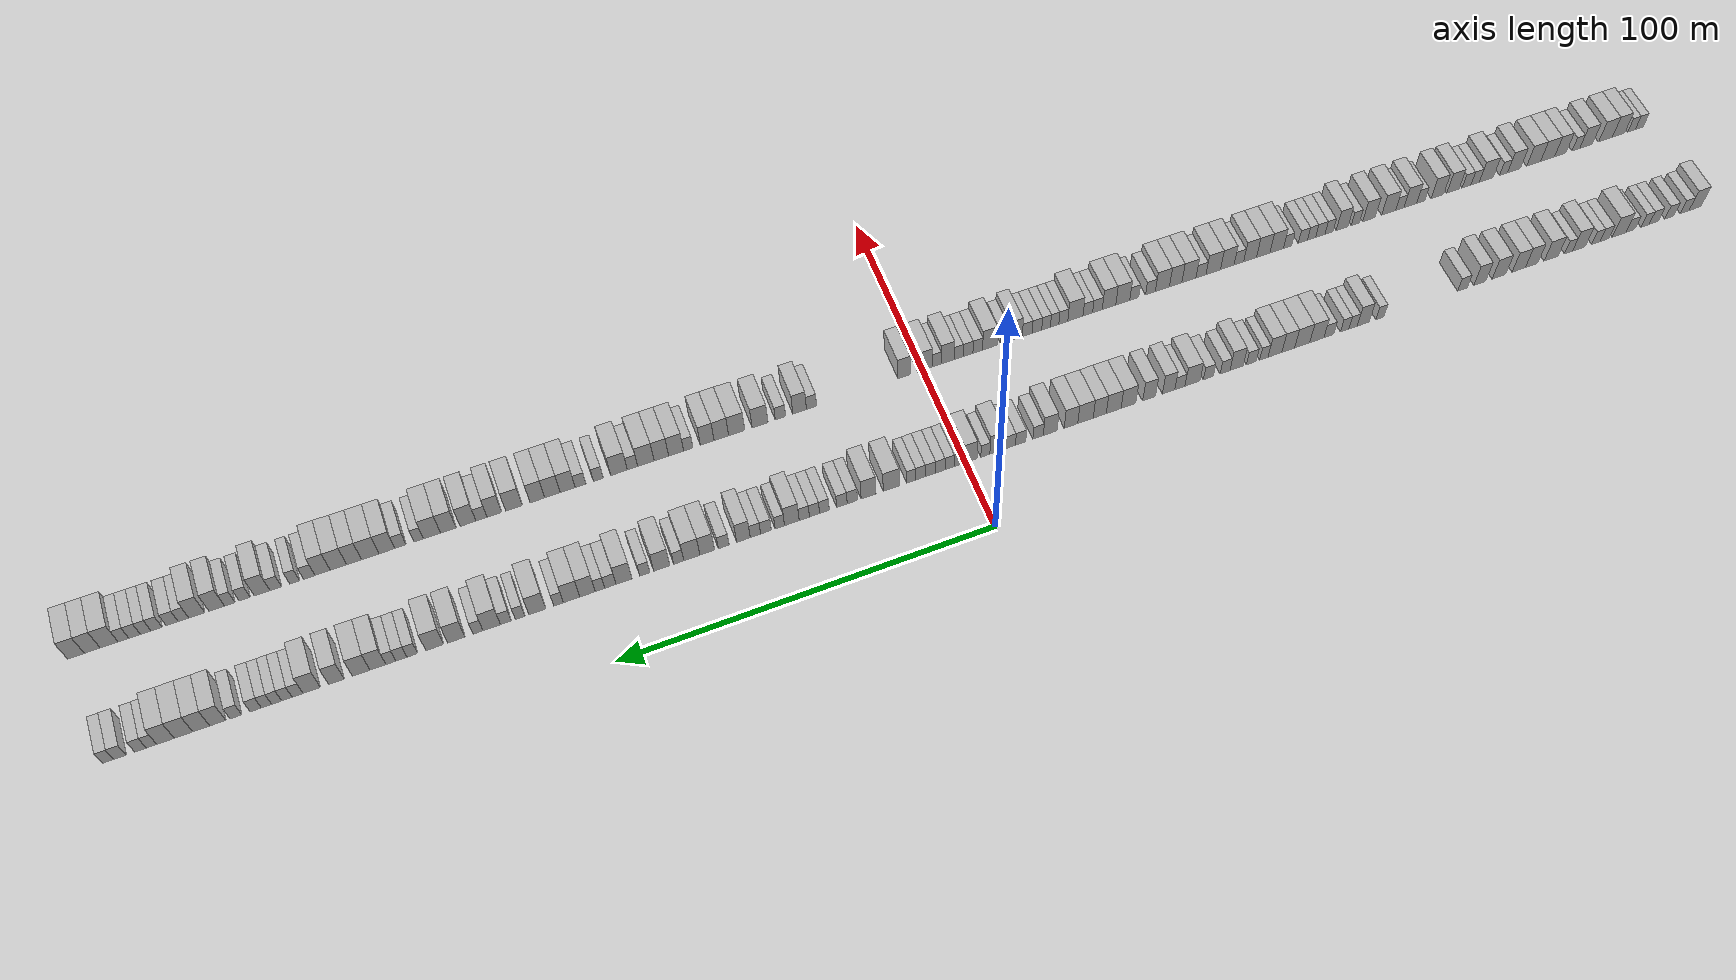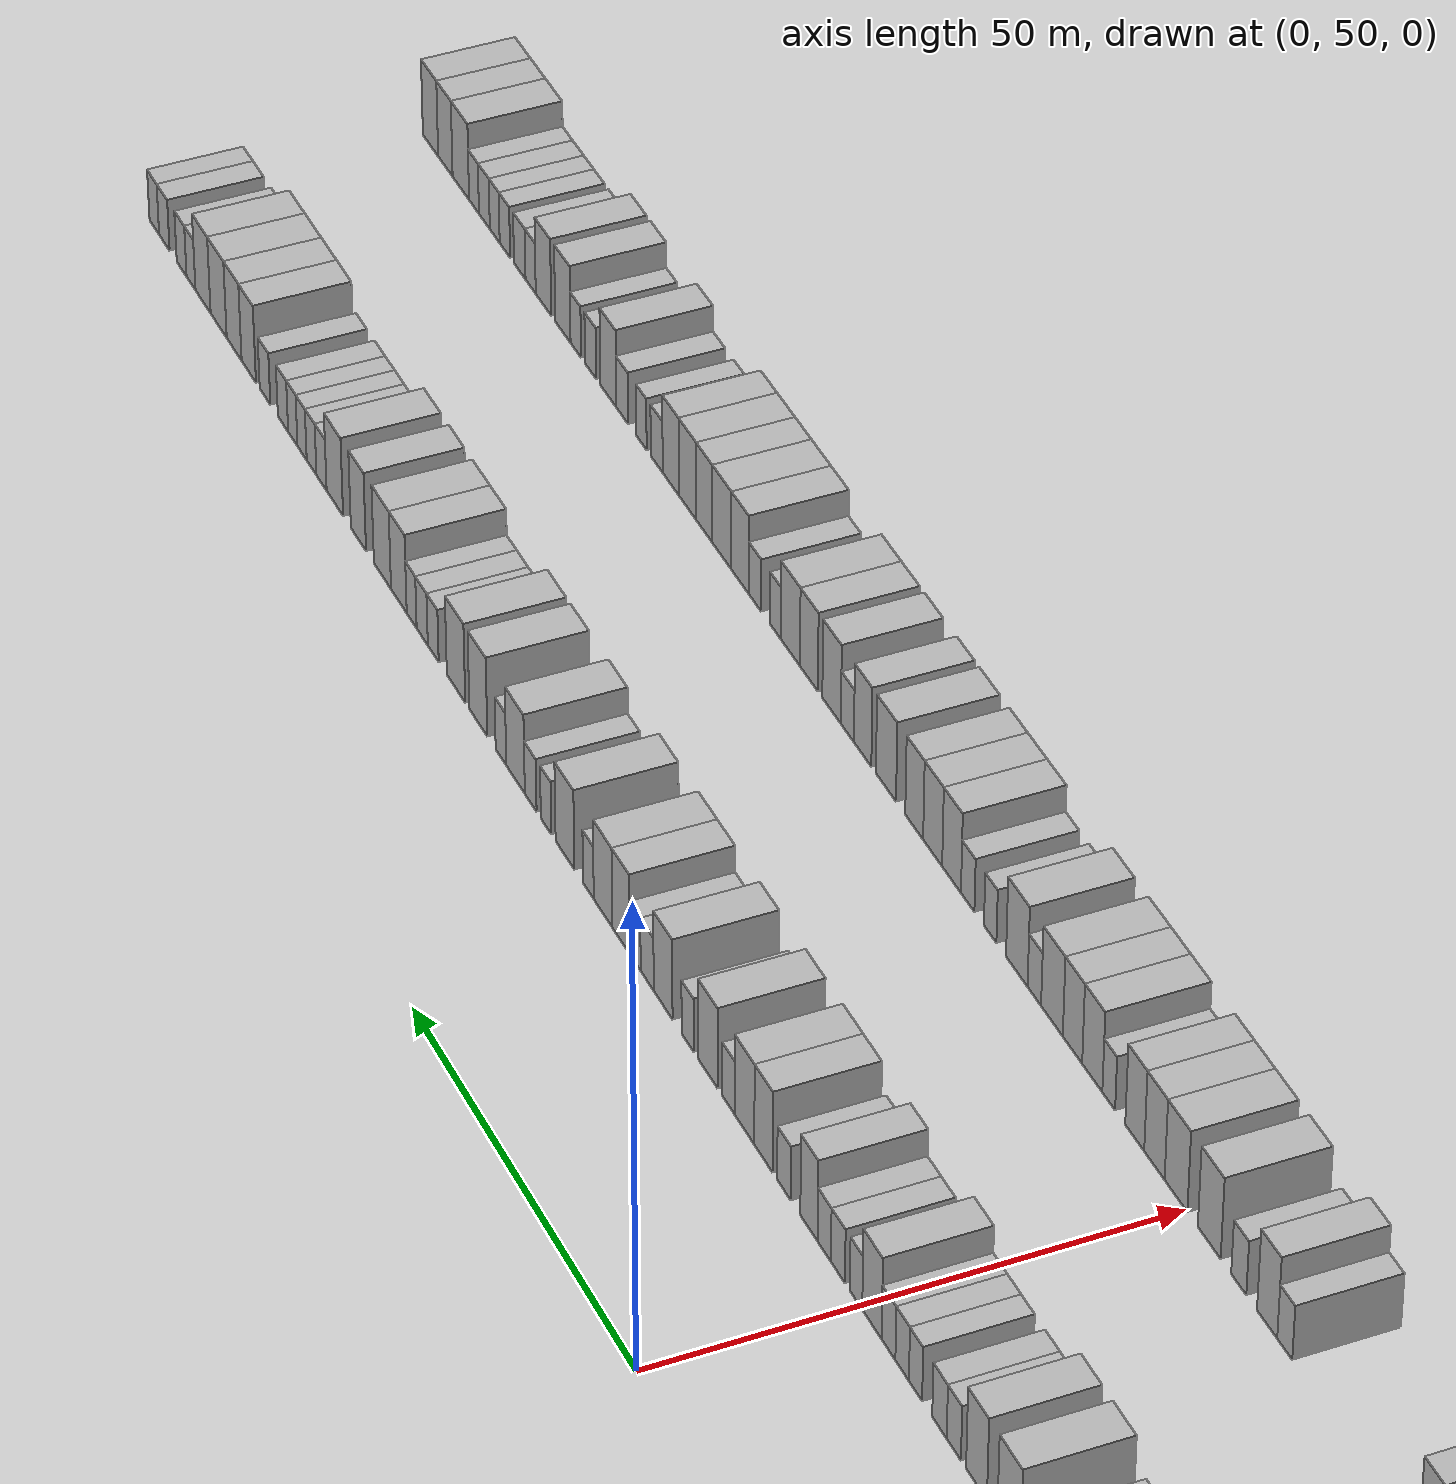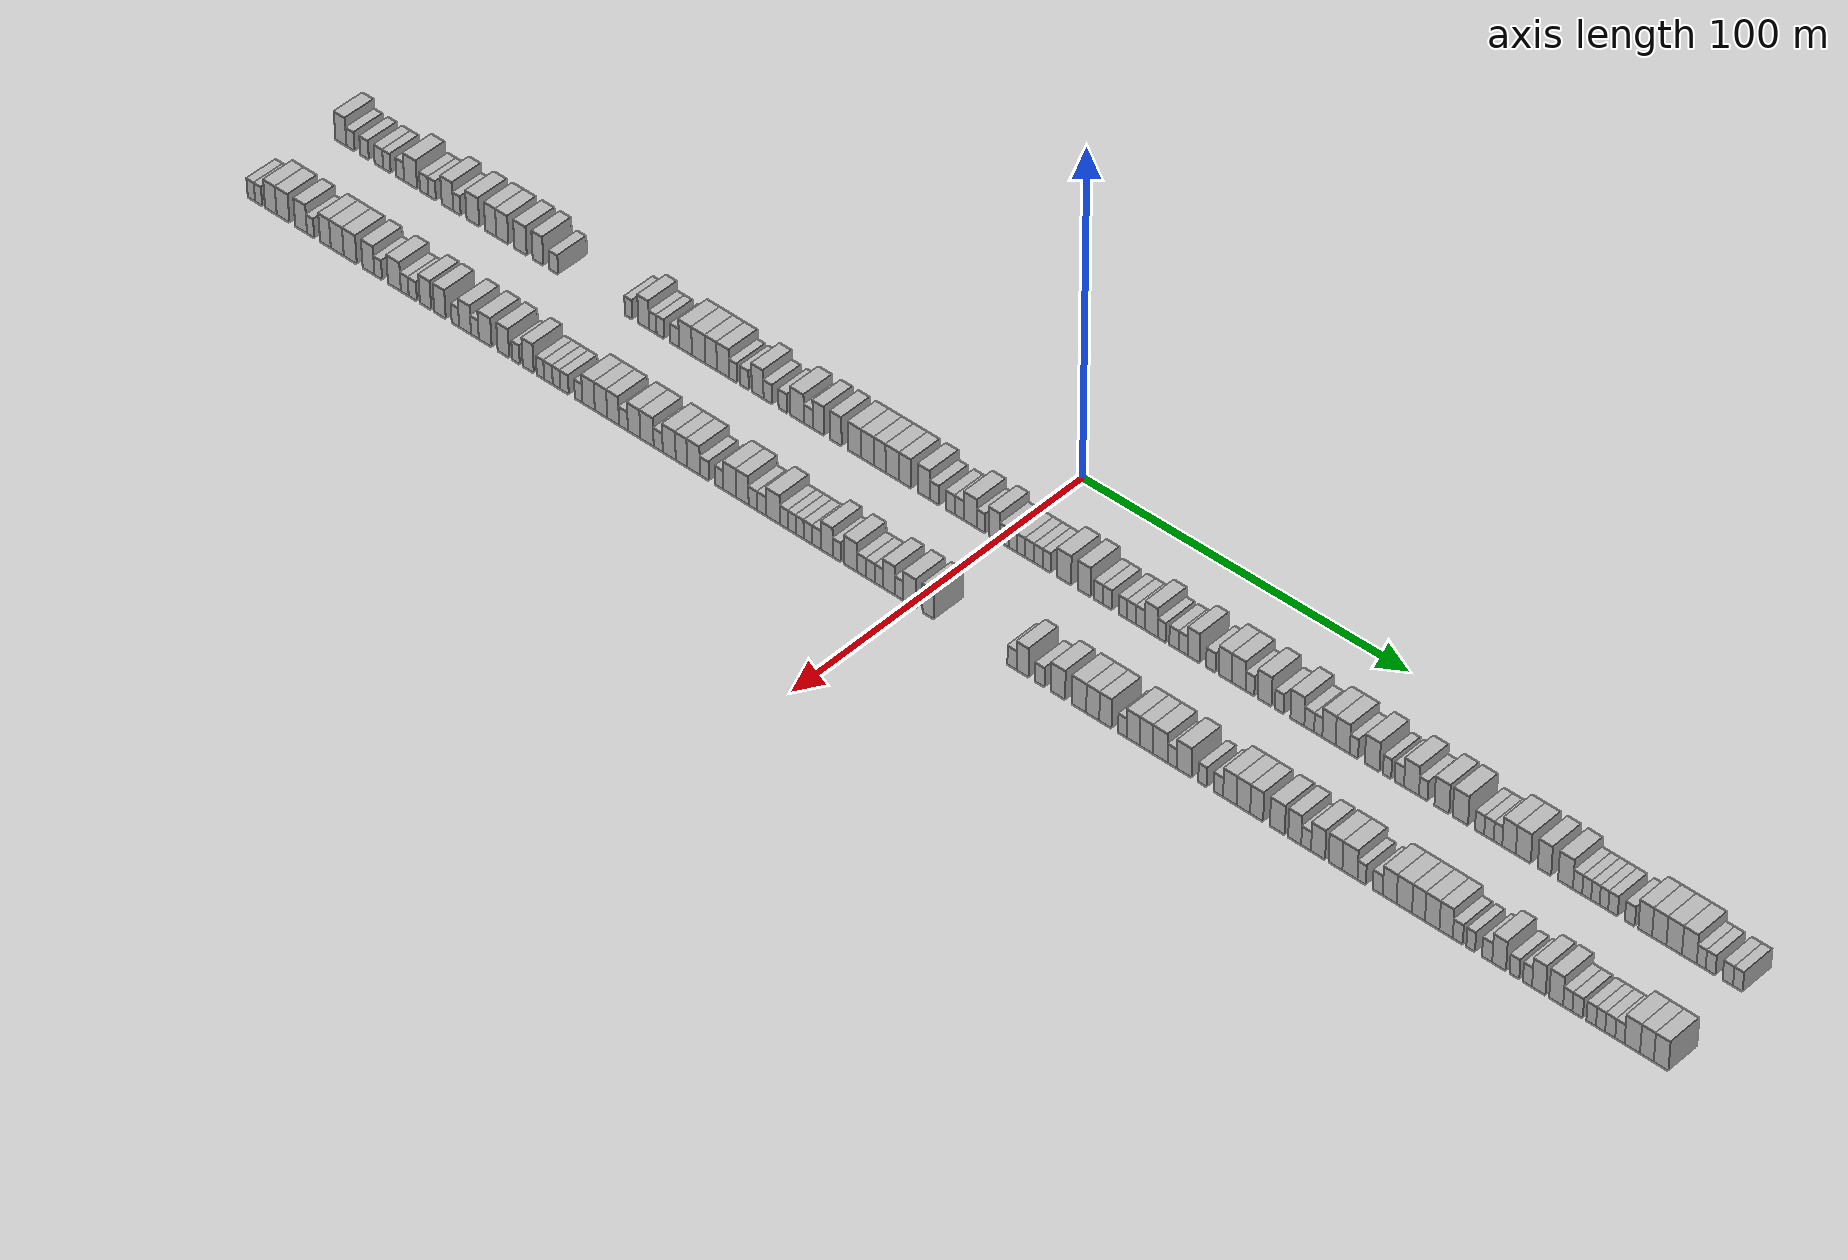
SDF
<sdf version="1.6">
 <world name="default">
  <scene>
   <sky><clouds><speed>12</speed></clouds></sky>
   <ambient>0.4 0.4 0.4 1</ambient>
   <background>0.7 0.7 0.7 1</background>
   <shadows>1</shadows>
  </scene>
  <gravity>0 0 -9.8066</gravity>
  <magnetic_field>6e-06 2.3e-05 -4.2e-05</magnetic_field>
  <physics default="0" name="default_physics" type="ode">
   <ode>
    <solver>
     <type>quick</type>
     <iters>10</iters>
     <sor>1.0</sor>
     <use_dynamic_moi_rescaling>0</use_dynamic_moi_rescaling>
    </solver>
    <constraints>
     <cfm>0</cfm>
     <erp>0.2</erp>
     <contact_max_correcting_vel>100</contact_max_correcting_vel>
     <contact_surface_layer>0.001</contact_surface_layer>
    </constraints>
   </ode>
   <max_step_size>0.004</max_step_size>
   <real_time_factor>1</real_time_factor>
   <real_time_update_rate>250</real_time_update_rate>
  </physics>
  <light name="sun" type="directional">
   <pose>0 0 10 0 0 0</pose>
   <diffuse>0.8 0.8 0.8 1</diffuse>
   <specular>0.2 0.2 0.2 1</specular>
   <attenuation>
    <range>1000</range>
    <constant>0.9</constant>
    <linear>0.01</linear>
    <quadratic>0.001</quadratic>
   </attenuation>
   <direction>-0.5 0.1 -0.9</direction>
  </light>
  <model name="building_1">
   <static>1</static>
   <pose>25.0000 -218.0600 0 0.000000 0.000000 0.000000</pose>
   <link name="link">
    <pose>0 0 4.50 0 0 0</pose>
    <collision name="collision"><geometry><box><size>10.0000 3.8800 9.0000</size></box></geometry></collision>
    <visual name="visual">
     <cast_shadows>0</cast_shadows>
     <geometry><box><size>10.0000 3.8800 9.0000</size></box></geometry>
     <material>
      <script>
       <uri>model://HANNAS_wall/materials/scripts</uri>
       <uri>model://HANNAS_wall/materials/textures</uri>
       <name>vrc/HANNAS_wall</name>
      </script>
     </material>
    </visual>
   </link>
  </model>
  <model name="building_2">
   <static>1</static>
   <pose>25.0000 -214.6943 0 0.000000 0.000000 0.000000</pose>
   <link name="link">
    <pose>0 0 3.00 0 0 0</pose>
    <collision name="collision"><geometry><box><size>10.0000 2.8513 6.0000</size></box></geometry></collision>
    <visual name="visual">
     <cast_shadows>0</cast_shadows>
     <geometry><box><size>10.0000 2.8513 6.0000</size></box></geometry>
     <material>
      <script>
       <uri>model://HANNAS_wall/materials/scripts</uri>
       <uri>model://HANNAS_wall/materials/textures</uri>
       <name>vrc/HANNAS_wall</name>
      </script>
     </material>
    </visual>
   </link>
  </model>
  <model name="building_3">
   <static>1</static>
   <pose>25.0000 -209.7895 0 0.000000 0.000000 0.000000</pose>
   <link name="link">
    <pose>0 0 3.00 0 0 0</pose>
    <collision name="collision"><geometry><box><size>10.0000 2.9583 6.0000</size></box></geometry></collision>
    <visual name="visual">
     <cast_shadows>0</cast_shadows>
     <geometry><box><size>10.0000 2.9583 6.0000</size></box></geometry>
     <material>
      <script>
       <uri>model://HANNAS_wall/materials/scripts</uri>
       <uri>model://HANNAS_wall/materials/textures</uri>
       <name>vrc/HANNAS_wall</name>
      </script>
     </material>
    </visual>
   </link>
  </model>
  <model name="building_4">
   <static>1</static>
   <pose>25.0000 -204.8114 0 0.000000 0.000000 0.000000</pose>
   <link name="link">
    <pose>0 0 3.00 0 0 0</pose>
    <collision name="collision"><geometry><box><size>10.0000 2.9979 6.0000</size></box></geometry></collision>
    <visual name="visual">
     <cast_shadows>0</cast_shadows>
     <geometry><box><size>10.0000 2.9979 6.0000</size></box></geometry>
     <material>
      <script>
       <uri>model://HANNAS_wall/materials/scripts</uri>
       <uri>model://HANNAS_wall/materials/textures</uri>
       <name>vrc/HANNAS_wall</name>
      </script>
     </material>
    </visual>
   </link>
  </model>
  <model name="building_5">
   <static>1</static>
   <pose>25.0000 -202.0157 0 0.000000 0.000000 0.000000</pose>
   <link name="link">
    <pose>0 0 3.00 0 0 0</pose>
    <collision name="collision"><geometry><box><size>10.0000 2.5935 6.0000</size></box></geometry></collision>
    <visual name="visual">
     <cast_shadows>0</cast_shadows>
     <geometry><box><size>10.0000 2.5935 6.0000</size></box></geometry>
     <material>
      <script>
       <uri>model://HANNAS_wall/materials/scripts</uri>
       <uri>model://HANNAS_wall/materials/textures</uri>
       <name>vrc/HANNAS_wall</name>
      </script>
     </material>
    </visual>
   </link>
  </model>
  <model name="building_6">
   <static>1</static>
   <pose>25.0000 -197.3693 0 0.000000 0.000000 0.000000</pose>
   <link name="link">
    <pose>0 0 3.00 0 0 0</pose>
    <collision name="collision"><geometry><box><size>10.0000 2.6991 6.0000</size></box></geometry></collision>
    <visual name="visual">
     <cast_shadows>0</cast_shadows>
     <geometry><box><size>10.0000 2.6991 6.0000</size></box></geometry>
     <material>
      <script>
       <uri>model://HANNAS_wall/materials/scripts</uri>
       <uri>model://HANNAS_wall/materials/textures</uri>
       <name>vrc/HANNAS_wall</name>
      </script>
     </material>
    </visual>
   </link>
  </model>
  <model name="building_7">
   <static>1</static>
   <pose>25.0000 -193.7817 0 0.000000 0.000000 0.000000</pose>
   <link name="link">
    <pose>0 0 4.50 0 0 0</pose>
    <collision name="collision"><geometry><box><size>10.0000 4.4761 9.0000</size></box></geometry></collision>
    <visual name="visual">
     <cast_shadows>0</cast_shadows>
     <geometry><box><size>10.0000 4.4761 9.0000</size></box></geometry>
     <material>
      <script>
       <uri>model://HANNAS_wall/materials/scripts</uri>
       <uri>model://HANNAS_wall/materials/textures</uri>
       <name>vrc/HANNAS_wall</name>
      </script>
     </material>
    </visual>
   </link>
  </model>
  <model name="building_8">
   <static>1</static>
   <pose>25.0000 -189.0932 0 0.000000 0.000000 0.000000</pose>
   <link name="link">
    <pose>0 0 3.00 0 0 0</pose>
    <collision name="collision"><geometry><box><size>10.0000 2.9010 6.0000</size></box></geometry></collision>
    <visual name="visual">
     <cast_shadows>0</cast_shadows>
     <geometry><box><size>10.0000 2.9010 6.0000</size></box></geometry>
     <material>
      <script>
       <uri>model://HANNAS_wall/materials/scripts</uri>
       <uri>model://HANNAS_wall/materials/textures</uri>
       <name>vrc/HANNAS_wall</name>
      </script>
     </material>
    </visual>
   </link>
  </model>
  <model name="building_9">
   <static>1</static>
   <pose>25.0000 -186.3501 0 0.000000 0.000000 0.000000</pose>
   <link name="link">
    <pose>0 0 3.00 0 0 0</pose>
    <collision name="collision"><geometry><box><size>10.0000 2.5852 6.0000</size></box></geometry></collision>
    <visual name="visual">
     <cast_shadows>0</cast_shadows>
     <geometry><box><size>10.0000 2.5852 6.0000</size></box></geometry>
     <material>
      <script>
       <uri>model://HANNAS_wall/materials/scripts</uri>
       <uri>model://HANNAS_wall/materials/textures</uri>
       <name>vrc/HANNAS_wall</name>
      </script>
     </material>
    </visual>
   </link>
  </model>
  <model name="building_10">
   <static>1</static>
   <pose>25.0000 -181.0532 0 0.000000 0.000000 0.000000</pose>
   <link name="link">
    <pose>0 0 4.50 0 0 0</pose>
    <collision name="collision"><geometry><box><size>10.0000 4.0086 9.0000</size></box></geometry></collision>
    <visual name="visual">
     <cast_shadows>0</cast_shadows>
     <geometry><box><size>10.0000 4.0086 9.0000</size></box></geometry>
     <material>
      <script>
       <uri>model://HANNAS_wall/materials/scripts</uri>
       <uri>model://HANNAS_wall/materials/textures</uri>
       <name>vrc/HANNAS_wall</name>
      </script>
     </material>
    </visual>
   </link>
  </model>
  <model name="building_11">
   <static>1</static>
   <pose>25.0000 -177.7852 0 0.000000 0.000000 0.000000</pose>
   <link name="link">
    <pose>0 0 3.00 0 0 0</pose>
    <collision name="collision"><geometry><box><size>10.0000 2.5274 6.0000</size></box></geometry></collision>
    <visual name="visual">
     <cast_shadows>0</cast_shadows>
     <geometry><box><size>10.0000 2.5274 6.0000</size></box></geometry>
     <material>
      <script>
       <uri>model://HANNAS_wall/materials/scripts</uri>
       <uri>model://HANNAS_wall/materials/textures</uri>
       <name>vrc/HANNAS_wall</name>
      </script>
     </material>
    </visual>
   </link>
  </model>
  <model name="building_12">
   <static>1</static>
   <pose>25.0000 -172.3337 0 0.000000 0.000000 0.000000</pose>
   <link name="link">
    <pose>0 0 4.50 0 0 0</pose>
    <collision name="collision"><geometry><box><size>10.0000 4.3756 9.0000</size></box></geometry></collision>
    <visual name="visual">
     <cast_shadows>0</cast_shadows>
     <geometry><box><size>10.0000 4.3756 9.0000</size></box></geometry>
     <material>
      <script>
       <uri>model://HANNAS_wall/materials/scripts</uri>
       <uri>model://HANNAS_wall/materials/textures</uri>
       <name>vrc/HANNAS_wall</name>
      </script>
     </material>
    </visual>
   </link>
  </model>
  <model name="building_13">
   <static>1</static>
   <pose>25.0000 -166.2220 0 0.000000 0.000000 0.000000</pose>
   <link name="link">
    <pose>0 0 4.50 0 0 0</pose>
    <collision name="collision"><geometry><box><size>10.0000 3.8479 9.0000</size></box></geometry></collision>
    <visual name="visual">
     <cast_shadows>0</cast_shadows>
     <geometry><box><size>10.0000 3.8479 9.0000</size></box></geometry>
     <material>
      <script>
       <uri>model://HANNAS_wall/materials/scripts</uri>
       <uri>model://HANNAS_wall/materials/textures</uri>
       <name>vrc/HANNAS_wall</name>
      </script>
     </material>
    </visual>
   </link>
  </model>
  <model name="building_14">
   <static>1</static>
   <pose>25.0000 -162.2357 0 0.000000 0.000000 0.000000</pose>
   <link name="link">
    <pose>0 0 4.50 0 0 0</pose>
    <collision name="collision"><geometry><box><size>10.0000 4.1246 9.0000</size></box></geometry></collision>
    <visual name="visual">
     <cast_shadows>0</cast_shadows>
     <geometry><box><size>10.0000 4.1246 9.0000</size></box></geometry>
     <material>
      <script>
       <uri>model://HANNAS_wall/materials/scripts</uri>
       <uri>model://HANNAS_wall/materials/textures</uri>
       <name>vrc/HANNAS_wall</name>
      </script>
     </material>
    </visual>
   </link>
  </model>
  <model name="building_15">
   <static>1</static>
   <pose>25.0000 -156.0748 0 0.000000 0.000000 0.000000</pose>
   <link name="link">
    <pose>0 0 4.50 0 0 0</pose>
    <collision name="collision"><geometry><box><size>10.0000 4.1973 9.0000</size></box></geometry></collision>
    <visual name="visual">
     <cast_shadows>0</cast_shadows>
     <geometry><box><size>10.0000 4.1973 9.0000</size></box></geometry>
     <material>
      <script>
       <uri>model://HANNAS_wall/materials/scripts</uri>
       <uri>model://HANNAS_wall/materials/textures</uri>
       <name>vrc/HANNAS_wall</name>
      </script>
     </material>
    </visual>
   </link>
  </model>
  <model name="building_16">
   <static>1</static>
   <pose>25.0000 -150.1493 0 0.000000 0.000000 0.000000</pose>
   <link name="link">
    <pose>0 0 4.50 0 0 0</pose>
    <collision name="collision"><geometry><box><size>10.0000 3.6537 9.0000</size></box></geometry></collision>
    <visual name="visual">
     <cast_shadows>0</cast_shadows>
     <geometry><box><size>10.0000 3.6537 9.0000</size></box></geometry>
     <material>
      <script>
       <uri>model://HANNAS_wall/materials/scripts</uri>
       <uri>model://HANNAS_wall/materials/textures</uri>
       <name>vrc/HANNAS_wall</name>
      </script>
     </material>
    </visual>
   </link>
  </model>
  <model name="building_17">
   <static>1</static>
   <pose>25.0000 -144.8333 0 0.000000 0.000000 0.000000</pose>
   <link name="link">
    <pose>0 0 3.00 0 0 0</pose>
    <collision name="collision"><geometry><box><size>10.0000 2.9784 6.0000</size></box></geometry></collision>
    <visual name="visual">
     <cast_shadows>0</cast_shadows>
     <geometry><box><size>10.0000 2.9784 6.0000</size></box></geometry>
     <material>
      <script>
       <uri>model://HANNAS_wall/materials/scripts</uri>
       <uri>model://HANNAS_wall/materials/textures</uri>
       <name>vrc/HANNAS_wall</name>
      </script>
     </material>
    </visual>
   </link>
  </model>
  <model name="building_18">
   <static>1</static>
   <pose>25.0000 -119.6848 0 0.000000 0.000000 0.000000</pose>
   <link name="link">
    <pose>0 0 3.00 0 0 0</pose>
    <collision name="collision"><geometry><box><size>10.0000 2.4395 6.0000</size></box></geometry></collision>
    <visual name="visual">
     <cast_shadows>0</cast_shadows>
     <geometry><box><size>10.0000 2.4395 6.0000</size></box></geometry>
     <material>
      <script>
       <uri>model://HANNAS_wall/materials/scripts</uri>
       <uri>model://HANNAS_wall/materials/textures</uri>
       <name>vrc/HANNAS_wall</name>
      </script>
     </material>
    </visual>
   </link>
  </model>
  <model name="building_19">
   <static>1</static>
   <pose>25.0000 -114.6445 0 0.000000 0.000000 0.000000</pose>
   <link name="link">
    <pose>0 0 4.50 0 0 0</pose>
    <collision name="collision"><geometry><box><size>10.0000 3.6411 9.0000</size></box></geometry></collision>
    <visual name="visual">
     <cast_shadows>0</cast_shadows>
     <geometry><box><size>10.0000 3.6411 9.0000</size></box></geometry>
     <material>
      <script>
       <uri>model://HANNAS_wall/materials/scripts</uri>
       <uri>model://HANNAS_wall/materials/textures</uri>
       <name>vrc/HANNAS_wall</name>
      </script>
     </material>
    </visual>
   </link>
  </model>
  <model name="building_20">
   <static>1</static>
   <pose>25.0000 -111.5989 0 0.000000 0.000000 0.000000</pose>
   <link name="link">
    <pose>0 0 3.00 0 0 0</pose>
    <collision name="collision"><geometry><box><size>10.0000 2.4501 6.0000</size></box></geometry></collision>
    <visual name="visual">
     <cast_shadows>0</cast_shadows>
     <geometry><box><size>10.0000 2.4501 6.0000</size></box></geometry>
     <material>
      <script>
       <uri>model://HANNAS_wall/materials/scripts</uri>
       <uri>model://HANNAS_wall/materials/textures</uri>
       <name>vrc/HANNAS_wall</name>
      </script>
     </material>
    </visual>
   </link>
  </model>
  <model name="building_21">
   <static>1</static>
   <pose>25.0000 -109.0927 0 0.000000 0.000000 0.000000</pose>
   <link name="link">
    <pose>0 0 3.00 0 0 0</pose>
    <collision name="collision"><geometry><box><size>10.0000 2.5622 6.0000</size></box></geometry></collision>
    <visual name="visual">
     <cast_shadows>0</cast_shadows>
     <geometry><box><size>10.0000 2.5622 6.0000</size></box></geometry>
     <material>
      <script>
       <uri>model://HANNAS_wall/materials/scripts</uri>
       <uri>model://HANNAS_wall/materials/textures</uri>
       <name>vrc/HANNAS_wall</name>
      </script>
     </material>
    </visual>
   </link>
  </model>
  <model name="building_22">
   <static>1</static>
   <pose>25.0000 -104.3438 0 0.000000 0.000000 0.000000</pose>
   <link name="link">
    <pose>0 0 3.00 0 0 0</pose>
    <collision name="collision"><geometry><box><size>10.0000 2.9356 6.0000</size></box></geometry></collision>
    <visual name="visual">
     <cast_shadows>0</cast_shadows>
     <geometry><box><size>10.0000 2.9356 6.0000</size></box></geometry>
     <material>
      <script>
       <uri>model://HANNAS_wall/materials/scripts</uri>
       <uri>model://HANNAS_wall/materials/textures</uri>
       <name>vrc/HANNAS_wall</name>
      </script>
     </material>
    </visual>
   </link>
  </model>
  <model name="building_23">
   <static>1</static>
   <pose>25.0000 -100.7516 0 0.000000 0.000000 0.000000</pose>
   <link name="link">
    <pose>0 0 4.50 0 0 0</pose>
    <collision name="collision"><geometry><box><size>10.0000 4.2489 9.0000</size></box></geometry></collision>
    <visual name="visual">
     <cast_shadows>0</cast_shadows>
     <geometry><box><size>10.0000 4.2489 9.0000</size></box></geometry>
     <material>
      <script>
       <uri>model://HANNAS_wall/materials/scripts</uri>
       <uri>model://HANNAS_wall/materials/textures</uri>
       <name>vrc/HANNAS_wall</name>
      </script>
     </material>
    </visual>
   </link>
  </model>
  <model name="building_24">
   <static>1</static>
   <pose>25.0000 -96.4063 0 0.000000 0.000000 0.000000</pose>
   <link name="link">
    <pose>0 0 4.50 0 0 0</pose>
    <collision name="collision"><geometry><box><size>10.0000 4.4418 9.0000</size></box></geometry></collision>
    <visual name="visual">
     <cast_shadows>0</cast_shadows>
     <geometry><box><size>10.0000 4.4418 9.0000</size></box></geometry>
     <material>
      <script>
       <uri>model://HANNAS_wall/materials/scripts</uri>
       <uri>model://HANNAS_wall/materials/textures</uri>
       <name>vrc/HANNAS_wall</name>
      </script>
     </material>
    </visual>
   </link>
  </model>
  <model name="building_25">
   <static>1</static>
   <pose>25.0000 -92.2871 0 0.000000 0.000000 0.000000</pose>
   <link name="link">
    <pose>0 0 4.50 0 0 0</pose>
    <collision name="collision"><geometry><box><size>10.0000 3.7966 9.0000</size></box></geometry></collision>
    <visual name="visual">
     <cast_shadows>0</cast_shadows>
     <geometry><box><size>10.0000 3.7966 9.0000</size></box></geometry>
     <material>
      <script>
       <uri>model://HANNAS_wall/materials/scripts</uri>
       <uri>model://HANNAS_wall/materials/textures</uri>
       <name>vrc/HANNAS_wall</name>
      </script>
     </material>
    </visual>
   </link>
  </model>
  <model name="building_26">
   <static>1</static>
   <pose>25.0000 -88.3463 0 0.000000 0.000000 0.000000</pose>
   <link name="link">
    <pose>0 0 4.50 0 0 0</pose>
    <collision name="collision"><geometry><box><size>10.0000 4.0851 9.0000</size></box></geometry></collision>
    <visual name="visual">
     <cast_shadows>0</cast_shadows>
     <geometry><box><size>10.0000 4.0851 9.0000</size></box></geometry>
     <material>
      <script>
       <uri>model://HANNAS_wall/materials/scripts</uri>
       <uri>model://HANNAS_wall/materials/textures</uri>
       <name>vrc/HANNAS_wall</name>
      </script>
     </material>
    </visual>
   </link>
  </model>
  <model name="building_27">
   <static>1</static>
   <pose>25.0000 -85.0613 0 0.000000 0.000000 0.000000</pose>
   <link name="link">
    <pose>0 0 3.00 0 0 0</pose>
    <collision name="collision"><geometry><box><size>10.0000 2.4848 6.0000</size></box></geometry></collision>
    <visual name="visual">
     <cast_shadows>0</cast_shadows>
     <geometry><box><size>10.0000 2.4848 6.0000</size></box></geometry>
     <material>
      <script>
       <uri>model://HANNAS_wall/materials/scripts</uri>
       <uri>model://HANNAS_wall/materials/textures</uri>
       <name>vrc/HANNAS_wall</name>
      </script>
     </material>
    </visual>
   </link>
  </model>
  <model name="building_28">
   <static>1</static>
   <pose>25.0000 -81.3855 0 0.000000 0.000000 0.000000</pose>
   <link name="link">
    <pose>0 0 3.00 0 0 0</pose>
    <collision name="collision"><geometry><box><size>10.0000 2.8669 6.0000</size></box></geometry></collision>
    <visual name="visual">
     <cast_shadows>0</cast_shadows>
     <geometry><box><size>10.0000 2.8669 6.0000</size></box></geometry>
     <material>
      <script>
       <uri>model://HANNAS_wall/materials/scripts</uri>
       <uri>model://HANNAS_wall/materials/textures</uri>
       <name>vrc/HANNAS_wall</name>
      </script>
     </material>
    </visual>
   </link>
  </model>
  <model name="building_29">
   <static>1</static>
   <pose>25.0000 -77.0299 0 0.000000 0.000000 0.000000</pose>
   <link name="link">
    <pose>0 0 4.50 0 0 0</pose>
    <collision name="collision"><geometry><box><size>10.0000 3.8443 9.0000</size></box></geometry></collision>
    <visual name="visual">
     <cast_shadows>0</cast_shadows>
     <geometry><box><size>10.0000 3.8443 9.0000</size></box></geometry>
     <material>
      <script>
       <uri>model://HANNAS_wall/materials/scripts</uri>
       <uri>model://HANNAS_wall/materials/textures</uri>
       <name>vrc/HANNAS_wall</name>
      </script>
     </material>
    </visual>
   </link>
  </model>
  <model name="building_30">
   <static>1</static>
   <pose>25.0000 -73.6719 0 0.000000 0.000000 0.000000</pose>
   <link name="link">
    <pose>0 0 3.00 0 0 0</pose>
    <collision name="collision"><geometry><box><size>10.0000 2.8716 6.0000</size></box></geometry></collision>
    <visual name="visual">
     <cast_shadows>0</cast_shadows>
     <geometry><box><size>10.0000 2.8716 6.0000</size></box></geometry>
     <material>
      <script>
       <uri>model://HANNAS_wall/materials/scripts</uri>
       <uri>model://HANNAS_wall/materials/textures</uri>
       <name>vrc/HANNAS_wall</name>
      </script>
     </material>
    </visual>
   </link>
  </model>
  <model name="building_31">
   <static>1</static>
   <pose>25.0000 -68.7926 0 0.000000 0.000000 0.000000</pose>
   <link name="link">
    <pose>0 0 3.00 0 0 0</pose>
    <collision name="collision"><geometry><box><size>10.0000 2.8871 6.0000</size></box></geometry></collision>
    <visual name="visual">
     <cast_shadows>0</cast_shadows>
     <geometry><box><size>10.0000 2.8871 6.0000</size></box></geometry>
     <material>
      <script>
       <uri>model://HANNAS_wall/materials/scripts</uri>
       <uri>model://HANNAS_wall/materials/textures</uri>
       <name>vrc/HANNAS_wall</name>
      </script>
     </material>
    </visual>
   </link>
  </model>
  <model name="building_32">
   <static>1</static>
   <pose>25.0000 -64.1638 0 0.000000 0.000000 0.000000</pose>
   <link name="link">
    <pose>0 0 4.50 0 0 0</pose>
    <collision name="collision"><geometry><box><size>10.0000 4.3705 9.0000</size></box></geometry></collision>
    <visual name="visual">
     <cast_shadows>0</cast_shadows>
     <geometry><box><size>10.0000 4.3705 9.0000</size></box></geometry>
     <material>
      <script>
       <uri>model://HANNAS_wall/materials/scripts</uri>
       <uri>model://HANNAS_wall/materials/textures</uri>
       <name>vrc/HANNAS_wall</name>
      </script>
     </material>
    </visual>
   </link>
  </model>
  <model name="building_33">
   <static>1</static>
   <pose>25.0000 -60.5266 0 0.000000 0.000000 0.000000</pose>
   <link name="link">
    <pose>0 0 3.00 0 0 0</pose>
    <collision name="collision"><geometry><box><size>10.0000 2.9038 6.0000</size></box></geometry></collision>
    <visual name="visual">
     <cast_shadows>0</cast_shadows>
     <geometry><box><size>10.0000 2.9038 6.0000</size></box></geometry>
     <material>
      <script>
       <uri>model://HANNAS_wall/materials/scripts</uri>
       <uri>model://HANNAS_wall/materials/textures</uri>
       <name>vrc/HANNAS_wall</name>
      </script>
     </material>
    </visual>
   </link>
  </model>
  <model name="building_34">
   <static>1</static>
   <pose>25.0000 -57.2650 0 0.000000 0.000000 0.000000</pose>
   <link name="link">
    <pose>0 0 4.50 0 0 0</pose>
    <collision name="collision"><geometry><box><size>10.0000 3.6195 9.0000</size></box></geometry></collision>
    <visual name="visual">
     <cast_shadows>0</cast_shadows>
     <geometry><box><size>10.0000 3.6195 9.0000</size></box></geometry>
     <material>
      <script>
       <uri>model://HANNAS_wall/materials/scripts</uri>
       <uri>model://HANNAS_wall/materials/textures</uri>
       <name>vrc/HANNAS_wall</name>
      </script>
     </material>
    </visual>
   </link>
  </model>
  <model name="building_35">
   <static>1</static>
   <pose>25.0000 -51.6210 0 0.000000 0.000000 0.000000</pose>
   <link name="link">
    <pose>0 0 4.50 0 0 0</pose>
    <collision name="collision"><geometry><box><size>10.0000 3.6685 9.0000</size></box></geometry></collision>
    <visual name="visual">
     <cast_shadows>0</cast_shadows>
     <geometry><box><size>10.0000 3.6685 9.0000</size></box></geometry>
     <material>
      <script>
       <uri>model://HANNAS_wall/materials/scripts</uri>
       <uri>model://HANNAS_wall/materials/textures</uri>
       <name>vrc/HANNAS_wall</name>
      </script>
     </material>
    </visual>
   </link>
  </model>
  <model name="building_36">
   <static>1</static>
   <pose>25.0000 -45.6863 0 0.000000 0.000000 0.000000</pose>
   <link name="link">
    <pose>0 0 4.50 0 0 0</pose>
    <collision name="collision"><geometry><box><size>10.0000 4.2008 9.0000</size></box></geometry></collision>
    <visual name="visual">
     <cast_shadows>0</cast_shadows>
     <geometry><box><size>10.0000 4.2008 9.0000</size></box></geometry>
     <material>
      <script>
       <uri>model://HANNAS_wall/materials/scripts</uri>
       <uri>model://HANNAS_wall/materials/textures</uri>
       <name>vrc/HANNAS_wall</name>
      </script>
     </material>
    </visual>
   </link>
  </model>
  <model name="building_37">
   <static>1</static>
   <pose>25.0000 -41.4699 0 0.000000 0.000000 0.000000</pose>
   <link name="link">
    <pose>0 0 4.50 0 0 0</pose>
    <collision name="collision"><geometry><box><size>10.0000 4.2320 9.0000</size></box></geometry></collision>
    <visual name="visual">
     <cast_shadows>0</cast_shadows>
     <geometry><box><size>10.0000 4.2320 9.0000</size></box></geometry>
     <material>
      <script>
       <uri>model://HANNAS_wall/materials/scripts</uri>
       <uri>model://HANNAS_wall/materials/textures</uri>
       <name>vrc/HANNAS_wall</name>
      </script>
     </material>
    </visual>
   </link>
  </model>
  <model name="building_38">
   <static>1</static>
   <pose>25.0000 -37.5011 0 0.000000 0.000000 0.000000</pose>
   <link name="link">
    <pose>0 0 4.50 0 0 0</pose>
    <collision name="collision"><geometry><box><size>10.0000 3.7056 9.0000</size></box></geometry></collision>
    <visual name="visual">
     <cast_shadows>0</cast_shadows>
     <geometry><box><size>10.0000 3.7056 9.0000</size></box></geometry>
     <material>
      <script>
       <uri>model://HANNAS_wall/materials/scripts</uri>
       <uri>model://HANNAS_wall/materials/textures</uri>
       <name>vrc/HANNAS_wall</name>
      </script>
     </material>
    </visual>
   </link>
  </model>
  <model name="building_39">
   <static>1</static>
   <pose>25.0000 -33.4567 0 0.000000 0.000000 0.000000</pose>
   <link name="link">
    <pose>0 0 4.50 0 0 0</pose>
    <collision name="collision"><geometry><box><size>10.0000 4.3831 9.0000</size></box></geometry></collision>
    <visual name="visual">
     <cast_shadows>0</cast_shadows>
     <geometry><box><size>10.0000 4.3831 9.0000</size></box></geometry>
     <material>
      <script>
       <uri>model://HANNAS_wall/materials/scripts</uri>
       <uri>model://HANNAS_wall/materials/textures</uri>
       <name>vrc/HANNAS_wall</name>
      </script>
     </material>
    </visual>
   </link>
  </model>
  <model name="building_40">
   <static>1</static>
   <pose>25.0000 -29.3415 0 0.000000 0.000000 0.000000</pose>
   <link name="link">
    <pose>0 0 4.50 0 0 0</pose>
    <collision name="collision"><geometry><box><size>10.0000 3.8474 9.0000</size></box></geometry></collision>
    <visual name="visual">
     <cast_shadows>0</cast_shadows>
     <geometry><box><size>10.0000 3.8474 9.0000</size></box></geometry>
     <material>
      <script>
       <uri>model://HANNAS_wall/materials/scripts</uri>
       <uri>model://HANNAS_wall/materials/textures</uri>
       <name>vrc/HANNAS_wall</name>
      </script>
     </material>
    </visual>
   </link>
  </model>
  <model name="building_41">
   <static>1</static>
   <pose>25.0000 -23.4718 0 0.000000 0.000000 0.000000</pose>
   <link name="link">
    <pose>0 0 4.50 0 0 0</pose>
    <collision name="collision"><geometry><box><size>10.0000 3.8921 9.0000</size></box></geometry></collision>
    <visual name="visual">
     <cast_shadows>0</cast_shadows>
     <geometry><box><size>10.0000 3.8921 9.0000</size></box></geometry>
     <material>
      <script>
       <uri>model://HANNAS_wall/materials/scripts</uri>
       <uri>model://HANNAS_wall/materials/textures</uri>
       <name>vrc/HANNAS_wall</name>
      </script>
     </material>
    </visual>
   </link>
  </model>
  <model name="building_42">
   <static>1</static>
   <pose>25.0000 -20.0502 0 0.000000 0.000000 0.000000</pose>
   <link name="link">
    <pose>0 0 3.00 0 0 0</pose>
    <collision name="collision"><geometry><box><size>10.0000 2.9510 6.0000</size></box></geometry></collision>
    <visual name="visual">
     <cast_shadows>0</cast_shadows>
     <geometry><box><size>10.0000 2.9510 6.0000</size></box></geometry>
     <material>
      <script>
       <uri>model://HANNAS_wall/materials/scripts</uri>
       <uri>model://HANNAS_wall/materials/textures</uri>
       <name>vrc/HANNAS_wall</name>
      </script>
     </material>
    </visual>
   </link>
  </model>
  <model name="building_43">
   <static>1</static>
   <pose>25.0000 -15.1370 0 0.000000 0.000000 0.000000</pose>
   <link name="link">
    <pose>0 0 3.00 0 0 0</pose>
    <collision name="collision"><geometry><box><size>10.0000 2.8754 6.0000</size></box></geometry></collision>
    <visual name="visual">
     <cast_shadows>0</cast_shadows>
     <geometry><box><size>10.0000 2.8754 6.0000</size></box></geometry>
     <material>
      <script>
       <uri>model://HANNAS_wall/materials/scripts</uri>
       <uri>model://HANNAS_wall/materials/textures</uri>
       <name>vrc/HANNAS_wall</name>
      </script>
     </material>
    </visual>
   </link>
  </model>
  <model name="building_44">
   <static>1</static>
   <pose>25.0000 -12.2270 0 0.000000 0.000000 0.000000</pose>
   <link name="link">
    <pose>0 0 3.00 0 0 0</pose>
    <collision name="collision"><geometry><box><size>10.0000 2.9447 6.0000</size></box></geometry></collision>
    <visual name="visual">
     <cast_shadows>0</cast_shadows>
     <geometry><box><size>10.0000 2.9447 6.0000</size></box></geometry>
     <material>
      <script>
       <uri>model://HANNAS_wall/materials/scripts</uri>
       <uri>model://HANNAS_wall/materials/textures</uri>
       <name>vrc/HANNAS_wall</name>
      </script>
     </material>
    </visual>
   </link>
  </model>
  <model name="building_45">
   <static>1</static>
   <pose>25.0000 -8.6451 0 0.000000 0.000000 0.000000</pose>
   <link name="link">
    <pose>0 0 4.50 0 0 0</pose>
    <collision name="collision"><geometry><box><size>10.0000 4.2191 9.0000</size></box></geometry></collision>
    <visual name="visual">
     <cast_shadows>0</cast_shadows>
     <geometry><box><size>10.0000 4.2191 9.0000</size></box></geometry>
     <material>
      <script>
       <uri>model://HANNAS_wall/materials/scripts</uri>
       <uri>model://HANNAS_wall/materials/textures</uri>
       <name>vrc/HANNAS_wall</name>
      </script>
     </material>
    </visual>
   </link>
  </model>
  <model name="building_46">
   <static>1</static>
   <pose>25.0000 -5.2755 0 0.000000 0.000000 0.000000</pose>
   <link name="link">
    <pose>0 0 3.00 0 0 0</pose>
    <collision name="collision"><geometry><box><size>10.0000 2.5201 6.0000</size></box></geometry></collision>
    <visual name="visual">
     <cast_shadows>0</cast_shadows>
     <geometry><box><size>10.0000 2.5201 6.0000</size></box></geometry>
     <material>
      <script>
       <uri>model://HANNAS_wall/materials/scripts</uri>
       <uri>model://HANNAS_wall/materials/textures</uri>
       <name>vrc/HANNAS_wall</name>
      </script>
     </material>
    </visual>
   </link>
  </model>
  <model name="building_47">
   <static>1</static>
   <pose>25.0000 -1.1833 0 0.000000 0.000000 0.000000</pose>
   <link name="link">
    <pose>0 0 4.50 0 0 0</pose>
    <collision name="collision"><geometry><box><size>10.0000 3.6642 9.0000</size></box></geometry></collision>
    <visual name="visual">
     <cast_shadows>0</cast_shadows>
     <geometry><box><size>10.0000 3.6642 9.0000</size></box></geometry>
     <material>
      <script>
       <uri>model://HANNAS_wall/materials/scripts</uri>
       <uri>model://HANNAS_wall/materials/textures</uri>
       <name>vrc/HANNAS_wall</name>
      </script>
     </material>
    </visual>
   </link>
  </model>
  <model name="building_48">
   <static>1</static>
   <pose>25.0000 2.0056 0 0.000000 0.000000 0.000000</pose>
   <link name="link">
    <pose>0 0 3.00 0 0 0</pose>
    <collision name="collision"><geometry><box><size>10.0000 2.7137 6.0000</size></box></geometry></collision>
    <visual name="visual">
     <cast_shadows>0</cast_shadows>
     <geometry><box><size>10.0000 2.7137 6.0000</size></box></geometry>
     <material>
      <script>
       <uri>model://HANNAS_wall/materials/scripts</uri>
       <uri>model://HANNAS_wall/materials/textures</uri>
       <name>vrc/HANNAS_wall</name>
      </script>
     </material>
    </visual>
   </link>
  </model>
  <model name="building_49">
   <static>1</static>
   <pose>25.0000 4.6381 0 0.000000 0.000000 0.000000</pose>
   <link name="link">
    <pose>0 0 3.00 0 0 0</pose>
    <collision name="collision"><geometry><box><size>10.0000 2.5514 6.0000</size></box></geometry></collision>
    <visual name="visual">
     <cast_shadows>0</cast_shadows>
     <geometry><box><size>10.0000 2.5514 6.0000</size></box></geometry>
     <material>
      <script>
       <uri>model://HANNAS_wall/materials/scripts</uri>
       <uri>model://HANNAS_wall/materials/textures</uri>
       <name>vrc/HANNAS_wall</name>
      </script>
     </material>
    </visual>
   </link>
  </model>
  <model name="building_50">
   <static>1</static>
   <pose>25.0000 7.1918 0 0.000000 0.000000 0.000000</pose>
   <link name="link">
    <pose>0 0 3.00 0 0 0</pose>
    <collision name="collision"><geometry><box><size>10.0000 2.5560 6.0000</size></box></geometry></collision>
    <visual name="visual">
     <cast_shadows>0</cast_shadows>
     <geometry><box><size>10.0000 2.5560 6.0000</size></box></geometry>
     <material>
      <script>
       <uri>model://HANNAS_wall/materials/scripts</uri>
       <uri>model://HANNAS_wall/materials/textures</uri>
       <name>vrc/HANNAS_wall</name>
      </script>
     </material>
    </visual>
   </link>
  </model>
  <model name="building_51">
   <static>1</static>
   <pose>25.0000 9.8835 0 0.000000 0.000000 0.000000</pose>
   <link name="link">
    <pose>0 0 3.00 0 0 0</pose>
    <collision name="collision"><geometry><box><size>10.0000 2.8274 6.0000</size></box></geometry></collision>
    <visual name="visual">
     <cast_shadows>0</cast_shadows>
     <geometry><box><size>10.0000 2.8274 6.0000</size></box></geometry>
     <material>
      <script>
       <uri>model://HANNAS_wall/materials/scripts</uri>
       <uri>model://HANNAS_wall/materials/textures</uri>
       <name>vrc/HANNAS_wall</name>
      </script>
     </material>
    </visual>
   </link>
  </model>
  <model name="building_52">
   <static>1</static>
   <pose>25.0000 12.6209 0 0.000000 0.000000 0.000000</pose>
   <link name="link">
    <pose>0 0 3.00 0 0 0</pose>
    <collision name="collision"><geometry><box><size>10.0000 2.6474 6.0000</size></box></geometry></collision>
    <visual name="visual">
     <cast_shadows>0</cast_shadows>
     <geometry><box><size>10.0000 2.6474 6.0000</size></box></geometry>
     <material>
      <script>
       <uri>model://HANNAS_wall/materials/scripts</uri>
       <uri>model://HANNAS_wall/materials/textures</uri>
       <name>vrc/HANNAS_wall</name>
      </script>
     </material>
    </visual>
   </link>
  </model>
  <model name="building_53">
   <static>1</static>
   <pose>25.0000 15.1925 0 0.000000 0.000000 0.000000</pose>
   <link name="link">
    <pose>0 0 3.00 0 0 0</pose>
    <collision name="collision"><geometry><box><size>10.0000 2.4960 6.0000</size></box></geometry></collision>
    <visual name="visual">
     <cast_shadows>0</cast_shadows>
     <geometry><box><size>10.0000 2.4960 6.0000</size></box></geometry>
     <material>
      <script>
       <uri>model://HANNAS_wall/materials/scripts</uri>
       <uri>model://HANNAS_wall/materials/textures</uri>
       <name>vrc/HANNAS_wall</name>
      </script>
     </material>
    </visual>
   </link>
  </model>
  <model name="building_54">
   <static>1</static>
   <pose>25.0000 20.6453 0 0.000000 0.000000 0.000000</pose>
   <link name="link">
    <pose>0 0 4.50 0 0 0</pose>
    <collision name="collision"><geometry><box><size>10.0000 4.4096 9.0000</size></box></geometry></collision>
    <visual name="visual">
     <cast_shadows>0</cast_shadows>
     <geometry><box><size>10.0000 4.4096 9.0000</size></box></geometry>
     <material>
      <script>
       <uri>model://HANNAS_wall/materials/scripts</uri>
       <uri>model://HANNAS_wall/materials/textures</uri>
       <name>vrc/HANNAS_wall</name>
      </script>
     </material>
    </visual>
   </link>
  </model>
  <model name="building_55">
   <static>1</static>
   <pose>25.0000 26.8684 0 0.000000 0.000000 0.000000</pose>
   <link name="link">
    <pose>0 0 4.50 0 0 0</pose>
    <collision name="collision"><geometry><box><size>10.0000 4.0366 9.0000</size></box></geometry></collision>
    <visual name="visual">
     <cast_shadows>0</cast_shadows>
     <geometry><box><size>10.0000 4.0366 9.0000</size></box></geometry>
     <material>
      <script>
       <uri>model://HANNAS_wall/materials/scripts</uri>
       <uri>model://HANNAS_wall/materials/textures</uri>
       <name>vrc/HANNAS_wall</name>
      </script>
     </material>
    </visual>
   </link>
  </model>
  <model name="building_56">
   <static>1</static>
   <pose>25.0000 31.2788 0 0.000000 0.000000 0.000000</pose>
   <link name="link">
    <pose>0 0 3.00 0 0 0</pose>
    <collision name="collision"><geometry><box><size>10.0000 2.7842 6.0000</size></box></geometry></collision>
    <visual name="visual">
     <cast_shadows>0</cast_shadows>
     <geometry><box><size>10.0000 2.7842 6.0000</size></box></geometry>
     <material>
      <script>
       <uri>model://HANNAS_wall/materials/scripts</uri>
       <uri>model://HANNAS_wall/materials/textures</uri>
       <name>vrc/HANNAS_wall</name>
      </script>
     </material>
    </visual>
   </link>
  </model>
  <model name="building_57">
   <static>1</static>
   <pose>25.0000 34.0920 0 0.000000 0.000000 0.000000</pose>
   <link name="link">
    <pose>0 0 3.00 0 0 0</pose>
    <collision name="collision"><geometry><box><size>10.0000 2.8422 6.0000</size></box></geometry></collision>
    <visual name="visual">
     <cast_shadows>0</cast_shadows>
     <geometry><box><size>10.0000 2.8422 6.0000</size></box></geometry>
     <material>
      <script>
       <uri>model://HANNAS_wall/materials/scripts</uri>
       <uri>model://HANNAS_wall/materials/textures</uri>
       <name>vrc/HANNAS_wall</name>
      </script>
     </material>
    </visual>
   </link>
  </model>
  <model name="building_58">
   <static>1</static>
   <pose>25.0000 38.8232 0 0.000000 0.000000 0.000000</pose>
   <link name="link">
    <pose>0 0 3.00 0 0 0</pose>
    <collision name="collision"><geometry><box><size>10.0000 2.6201 6.0000</size></box></geometry></collision>
    <visual name="visual">
     <cast_shadows>0</cast_shadows>
     <geometry><box><size>10.0000 2.6201 6.0000</size></box></geometry>
     <material>
      <script>
       <uri>model://HANNAS_wall/materials/scripts</uri>
       <uri>model://HANNAS_wall/materials/textures</uri>
       <name>vrc/HANNAS_wall</name>
      </script>
     </material>
    </visual>
   </link>
  </model>
  <model name="building_59">
   <static>1</static>
   <pose>25.0000 41.4877 0 0.000000 0.000000 0.000000</pose>
   <link name="link">
    <pose>0 0 3.00 0 0 0</pose>
    <collision name="collision"><geometry><box><size>10.0000 2.7090 6.0000</size></box></geometry></collision>
    <visual name="visual">
     <cast_shadows>0</cast_shadows>
     <geometry><box><size>10.0000 2.7090 6.0000</size></box></geometry>
     <material>
      <script>
       <uri>model://HANNAS_wall/materials/scripts</uri>
       <uri>model://HANNAS_wall/materials/textures</uri>
       <name>vrc/HANNAS_wall</name>
      </script>
     </material>
    </visual>
   </link>
  </model>
  <model name="building_60">
   <static>1</static>
   <pose>25.0000 44.2271 0 0.000000 0.000000 0.000000</pose>
   <link name="link">
    <pose>0 0 3.00 0 0 0</pose>
    <collision name="collision"><geometry><box><size>10.0000 2.7699 6.0000</size></box></geometry></collision>
    <visual name="visual">
     <cast_shadows>0</cast_shadows>
     <geometry><box><size>10.0000 2.7699 6.0000</size></box></geometry>
     <material>
      <script>
       <uri>model://HANNAS_wall/materials/scripts</uri>
       <uri>model://HANNAS_wall/materials/textures</uri>
       <name>vrc/HANNAS_wall</name>
      </script>
     </material>
    </visual>
   </link>
  </model>
  <model name="building_61">
   <static>1</static>
   <pose>25.0000 47.5703 0 0.000000 0.000000 0.000000</pose>
   <link name="link">
    <pose>0 0 4.50 0 0 0</pose>
    <collision name="collision"><geometry><box><size>10.0000 3.9163 9.0000</size></box></geometry></collision>
    <visual name="visual">
     <cast_shadows>0</cast_shadows>
     <geometry><box><size>10.0000 3.9163 9.0000</size></box></geometry>
     <material>
      <script>
       <uri>model://HANNAS_wall/materials/scripts</uri>
       <uri>model://HANNAS_wall/materials/textures</uri>
       <name>vrc/HANNAS_wall</name>
      </script>
     </material>
    </visual>
   </link>
  </model>
  <model name="building_62">
   <static>1</static>
   <pose>25.0000 50.7920 0 0.000000 0.000000 0.000000</pose>
   <link name="link">
    <pose>0 0 3.00 0 0 0</pose>
    <collision name="collision"><geometry><box><size>10.0000 2.5271 6.0000</size></box></geometry></collision>
    <visual name="visual">
     <cast_shadows>0</cast_shadows>
     <geometry><box><size>10.0000 2.5271 6.0000</size></box></geometry>
     <material>
      <script>
       <uri>model://HANNAS_wall/materials/scripts</uri>
       <uri>model://HANNAS_wall/materials/textures</uri>
       <name>vrc/HANNAS_wall</name>
      </script>
     </material>
    </visual>
   </link>
  </model>
  <model name="building_63">
   <static>1</static>
   <pose>25.0000 54.4935 0 0.000000 0.000000 0.000000</pose>
   <link name="link">
    <pose>0 0 3.00 0 0 0</pose>
    <collision name="collision"><geometry><box><size>10.0000 2.8759 6.0000</size></box></geometry></collision>
    <visual name="visual">
     <cast_shadows>0</cast_shadows>
     <geometry><box><size>10.0000 2.8759 6.0000</size></box></geometry>
     <material>
      <script>
       <uri>model://HANNAS_wall/materials/scripts</uri>
       <uri>model://HANNAS_wall/materials/textures</uri>
       <name>vrc/HANNAS_wall</name>
      </script>
     </material>
    </visual>
   </link>
  </model>
  <model name="building_64">
   <static>1</static>
   <pose>25.0000 57.3033 0 0.000000 0.000000 0.000000</pose>
   <link name="link">
    <pose>0 0 3.00 0 0 0</pose>
    <collision name="collision"><geometry><box><size>10.0000 2.7436 6.0000</size></box></geometry></collision>
    <visual name="visual">
     <cast_shadows>0</cast_shadows>
     <geometry><box><size>10.0000 2.7436 6.0000</size></box></geometry>
     <material>
      <script>
       <uri>model://HANNAS_wall/materials/scripts</uri>
       <uri>model://HANNAS_wall/materials/textures</uri>
       <name>vrc/HANNAS_wall</name>
      </script>
     </material>
    </visual>
   </link>
  </model>
  <model name="building_65">
   <static>1</static>
   <pose>25.0000 60.4781 0 0.000000 0.000000 0.000000</pose>
   <link name="link">
    <pose>0 0 4.50 0 0 0</pose>
    <collision name="collision"><geometry><box><size>10.0000 3.6060 9.0000</size></box></geometry></collision>
    <visual name="visual">
     <cast_shadows>0</cast_shadows>
     <geometry><box><size>10.0000 3.6060 9.0000</size></box></geometry>
     <material>
      <script>
       <uri>model://HANNAS_wall/materials/scripts</uri>
       <uri>model://HANNAS_wall/materials/textures</uri>
       <name>vrc/HANNAS_wall</name>
      </script>
     </material>
    </visual>
   </link>
  </model>
  <model name="building_66">
   <static>1</static>
   <pose>25.0000 65.7047 0 0.000000 0.000000 0.000000</pose>
   <link name="link">
    <pose>0 0 3.00 0 0 0</pose>
    <collision name="collision"><geometry><box><size>10.0000 2.8471 6.0000</size></box></geometry></collision>
    <visual name="visual">
     <cast_shadows>0</cast_shadows>
     <geometry><box><size>10.0000 2.8471 6.0000</size></box></geometry>
     <material>
      <script>
       <uri>model://HANNAS_wall/materials/scripts</uri>
       <uri>model://HANNAS_wall/materials/textures</uri>
       <name>vrc/HANNAS_wall</name>
      </script>
     </material>
    </visual>
   </link>
  </model>
  <model name="building_67">
   <static>1</static>
   <pose>25.0000 70.0559 0 0.000000 0.000000 0.000000</pose>
   <link name="link">
    <pose>0 0 4.50 0 0 0</pose>
    <collision name="collision"><geometry><box><size>10.0000 3.8553 9.0000</size></box></geometry></collision>
    <visual name="visual">
     <cast_shadows>0</cast_shadows>
     <geometry><box><size>10.0000 3.8553 9.0000</size></box></geometry>
     <material>
      <script>
       <uri>model://HANNAS_wall/materials/scripts</uri>
       <uri>model://HANNAS_wall/materials/textures</uri>
       <name>vrc/HANNAS_wall</name>
      </script>
     </material>
    </visual>
   </link>
  </model>
  <model name="building_68">
   <static>1</static>
   <pose>25.0000 74.1039 0 0.000000 0.000000 0.000000</pose>
   <link name="link">
    <pose>0 0 4.50 0 0 0</pose>
    <collision name="collision"><geometry><box><size>10.0000 4.2406 9.0000</size></box></geometry></collision>
    <visual name="visual">
     <cast_shadows>0</cast_shadows>
     <geometry><box><size>10.0000 4.2406 9.0000</size></box></geometry>
     <material>
      <script>
       <uri>model://HANNAS_wall/materials/scripts</uri>
       <uri>model://HANNAS_wall/materials/textures</uri>
       <name>vrc/HANNAS_wall</name>
      </script>
     </material>
    </visual>
   </link>
  </model>
  <model name="building_69">
   <static>1</static>
   <pose>25.0000 77.5489 0 0.000000 0.000000 0.000000</pose>
   <link name="link">
    <pose>0 0 3.00 0 0 0</pose>
    <collision name="collision"><geometry><box><size>10.0000 2.6495 6.0000</size></box></geometry></collision>
    <visual name="visual">
     <cast_shadows>0</cast_shadows>
     <geometry><box><size>10.0000 2.6495 6.0000</size></box></geometry>
     <material>
      <script>
       <uri>model://HANNAS_wall/materials/scripts</uri>
       <uri>model://HANNAS_wall/materials/textures</uri>
       <name>vrc/HANNAS_wall</name>
      </script>
     </material>
    </visual>
   </link>
  </model>
  <model name="building_70">
   <static>1</static>
   <pose>25.0000 81.9790 0 0.000000 0.000000 0.000000</pose>
   <link name="link">
    <pose>0 0 4.50 0 0 0</pose>
    <collision name="collision"><geometry><box><size>10.0000 4.2107 9.0000</size></box></geometry></collision>
    <visual name="visual">
     <cast_shadows>0</cast_shadows>
     <geometry><box><size>10.0000 4.2107 9.0000</size></box></geometry>
     <material>
      <script>
       <uri>model://HANNAS_wall/materials/scripts</uri>
       <uri>model://HANNAS_wall/materials/textures</uri>
       <name>vrc/HANNAS_wall</name>
      </script>
     </material>
    </visual>
   </link>
  </model>
  <model name="building_71">
   <static>1</static>
   <pose>25.0000 86.4063 0 0.000000 0.000000 0.000000</pose>
   <link name="link">
    <pose>0 0 3.00 0 0 0</pose>
    <collision name="collision"><geometry><box><size>10.0000 2.6438 6.0000</size></box></geometry></collision>
    <visual name="visual">
     <cast_shadows>0</cast_shadows>
     <geometry><box><size>10.0000 2.6438 6.0000</size></box></geometry>
     <material>
      <script>
       <uri>model://HANNAS_wall/materials/scripts</uri>
       <uri>model://HANNAS_wall/materials/textures</uri>
       <name>vrc/HANNAS_wall</name>
      </script>
     </material>
    </visual>
   </link>
  </model>
  <model name="building_72">
   <static>1</static>
   <pose>25.0000 91.8164 0 0.000000 0.000000 0.000000</pose>
   <link name="link">
    <pose>0 0 4.50 0 0 0</pose>
    <collision name="collision"><geometry><box><size>10.0000 4.1764 9.0000</size></box></geometry></collision>
    <visual name="visual">
     <cast_shadows>0</cast_shadows>
     <geometry><box><size>10.0000 4.1764 9.0000</size></box></geometry>
     <material>
      <script>
       <uri>model://HANNAS_wall/materials/scripts</uri>
       <uri>model://HANNAS_wall/materials/textures</uri>
       <name>vrc/HANNAS_wall</name>
      </script>
     </material>
    </visual>
   </link>
  </model>
  <model name="building_73">
   <static>1</static>
   <pose>25.0000 95.3622 0 0.000000 0.000000 0.000000</pose>
   <link name="link">
    <pose>0 0 3.00 0 0 0</pose>
    <collision name="collision"><geometry><box><size>10.0000 2.9153 6.0000</size></box></geometry></collision>
    <visual name="visual">
     <cast_shadows>0</cast_shadows>
     <geometry><box><size>10.0000 2.9153 6.0000</size></box></geometry>
     <material>
      <script>
       <uri>model://HANNAS_wall/materials/scripts</uri>
       <uri>model://HANNAS_wall/materials/textures</uri>
       <name>vrc/HANNAS_wall</name>
      </script>
     </material>
    </visual>
   </link>
  </model>
  <model name="building_74">
   <static>1</static>
   <pose>25.0000 98.0449 0 0.000000 0.000000 0.000000</pose>
   <link name="link">
    <pose>0 0 3.00 0 0 0</pose>
    <collision name="collision"><geometry><box><size>10.0000 2.4500 6.0000</size></box></geometry></collision>
    <visual name="visual">
     <cast_shadows>0</cast_shadows>
     <geometry><box><size>10.0000 2.4500 6.0000</size></box></geometry>
     <material>
      <script>
       <uri>model://HANNAS_wall/materials/scripts</uri>
       <uri>model://HANNAS_wall/materials/textures</uri>
       <name>vrc/HANNAS_wall</name>
      </script>
     </material>
    </visual>
   </link>
  </model>
  <model name="building_75">
   <static>1</static>
   <pose>25.0000 101.2486 0 0.000000 0.000000 0.000000</pose>
   <link name="link">
    <pose>0 0 4.50 0 0 0</pose>
    <collision name="collision"><geometry><box><size>10.0000 3.9574 9.0000</size></box></geometry></collision>
    <visual name="visual">
     <cast_shadows>0</cast_shadows>
     <geometry><box><size>10.0000 3.9574 9.0000</size></box></geometry>
     <material>
      <script>
       <uri>model://HANNAS_wall/materials/scripts</uri>
       <uri>model://HANNAS_wall/materials/textures</uri>
       <name>vrc/HANNAS_wall</name>
      </script>
     </material>
    </visual>
   </link>
  </model>
  <model name="building_76">
   <static>1</static>
   <pose>25.0000 105.3379 0 0.000000 0.000000 0.000000</pose>
   <link name="link">
    <pose>0 0 4.50 0 0 0</pose>
    <collision name="collision"><geometry><box><size>10.0000 4.2212 9.0000</size></box></geometry></collision>
    <visual name="visual">
     <cast_shadows>0</cast_shadows>
     <geometry><box><size>10.0000 4.2212 9.0000</size></box></geometry>
     <material>
      <script>
       <uri>model://HANNAS_wall/materials/scripts</uri>
       <uri>model://HANNAS_wall/materials/textures</uri>
       <name>vrc/HANNAS_wall</name>
      </script>
     </material>
    </visual>
   </link>
  </model>
  <model name="building_77">
   <static>1</static>
   <pose>25.0000 108.6724 0 0.000000 0.000000 0.000000</pose>
   <link name="link">
    <pose>0 0 3.00 0 0 0</pose>
    <collision name="collision"><geometry><box><size>10.0000 2.4478 6.0000</size></box></geometry></collision>
    <visual name="visual">
     <cast_shadows>0</cast_shadows>
     <geometry><box><size>10.0000 2.4478 6.0000</size></box></geometry>
     <material>
      <script>
       <uri>model://HANNAS_wall/materials/scripts</uri>
       <uri>model://HANNAS_wall/materials/textures</uri>
       <name>vrc/HANNAS_wall</name>
      </script>
     </material>
    </visual>
   </link>
  </model>
  <model name="building_78">
   <static>1</static>
   <pose>25.0000 114.0790 0 0.000000 0.000000 0.000000</pose>
   <link name="link">
    <pose>0 0 4.50 0 0 0</pose>
    <collision name="collision"><geometry><box><size>10.0000 4.3654 9.0000</size></box></geometry></collision>
    <visual name="visual">
     <cast_shadows>0</cast_shadows>
     <geometry><box><size>10.0000 4.3654 9.0000</size></box></geometry>
     <material>
      <script>
       <uri>model://HANNAS_wall/materials/scripts</uri>
       <uri>model://HANNAS_wall/materials/textures</uri>
       <name>vrc/HANNAS_wall</name>
      </script>
     </material>
    </visual>
   </link>
  </model>
  <model name="building_79">
   <static>1</static>
   <pose>25.0000 118.4874 0 0.000000 0.000000 0.000000</pose>
   <link name="link">
    <pose>0 0 3.00 0 0 0</pose>
    <collision name="collision"><geometry><box><size>10.0000 2.4514 6.0000</size></box></geometry></collision>
    <visual name="visual">
     <cast_shadows>0</cast_shadows>
     <geometry><box><size>10.0000 2.4514 6.0000</size></box></geometry>
     <material>
      <script>
       <uri>model://HANNAS_wall/materials/scripts</uri>
       <uri>model://HANNAS_wall/materials/textures</uri>
       <name>vrc/HANNAS_wall</name>
      </script>
     </material>
    </visual>
   </link>
  </model>
  <model name="building_80">
   <static>1</static>
   <pose>25.0000 122.0968 0 0.000000 0.000000 0.000000</pose>
   <link name="link">
    <pose>0 0 3.00 0 0 0</pose>
    <collision name="collision"><geometry><box><size>10.0000 2.7674 6.0000</size></box></geometry></collision>
    <visual name="visual">
     <cast_shadows>0</cast_shadows>
     <geometry><box><size>10.0000 2.7674 6.0000</size></box></geometry>
     <material>
      <script>
       <uri>model://HANNAS_wall/materials/scripts</uri>
       <uri>model://HANNAS_wall/materials/textures</uri>
       <name>vrc/HANNAS_wall</name>
      </script>
     </material>
    </visual>
   </link>
  </model>
  <model name="building_81">
   <static>1</static>
   <pose>25.0000 125.6813 0 0.000000 0.000000 0.000000</pose>
   <link name="link">
    <pose>0 0 4.50 0 0 0</pose>
    <collision name="collision"><geometry><box><size>10.0000 4.4017 9.0000</size></box></geometry></collision>
    <visual name="visual">
     <cast_shadows>0</cast_shadows>
     <geometry><box><size>10.0000 4.4017 9.0000</size></box></geometry>
     <material>
      <script>
       <uri>model://HANNAS_wall/materials/scripts</uri>
       <uri>model://HANNAS_wall/materials/textures</uri>
       <name>vrc/HANNAS_wall</name>
      </script>
     </material>
    </visual>
   </link>
  </model>
  <model name="building_82">
   <static>1</static>
   <pose>25.0000 129.1506 0 0.000000 0.000000 0.000000</pose>
   <link name="link">
    <pose>0 0 3.00 0 0 0</pose>
    <collision name="collision"><geometry><box><size>10.0000 2.5369 6.0000</size></box></geometry></collision>
    <visual name="visual">
     <cast_shadows>0</cast_shadows>
     <geometry><box><size>10.0000 2.5369 6.0000</size></box></geometry>
     <material>
      <script>
       <uri>model://HANNAS_wall/materials/scripts</uri>
       <uri>model://HANNAS_wall/materials/textures</uri>
       <name>vrc/HANNAS_wall</name>
      </script>
     </material>
    </visual>
   </link>
  </model>
  <model name="building_83">
   <static>1</static>
   <pose>25.0000 134.5906 0 0.000000 0.000000 0.000000</pose>
   <link name="link">
    <pose>0 0 4.50 0 0 0</pose>
    <collision name="collision"><geometry><box><size>10.0000 4.3431 9.0000</size></box></geometry></collision>
    <visual name="visual">
     <cast_shadows>0</cast_shadows>
     <geometry><box><size>10.0000 4.3431 9.0000</size></box></geometry>
     <material>
      <script>
       <uri>model://HANNAS_wall/materials/scripts</uri>
       <uri>model://HANNAS_wall/materials/textures</uri>
       <name>vrc/HANNAS_wall</name>
      </script>
     </material>
    </visual>
   </link>
  </model>
  <model name="building_84">
   <static>1</static>
   <pose>25.0000 140.0104 0 0.000000 0.000000 0.000000</pose>
   <link name="link">
    <pose>0 0 4.50 0 0 0</pose>
    <collision name="collision"><geometry><box><size>10.0000 4.4965 9.0000</size></box></geometry></collision>
    <visual name="visual">
     <cast_shadows>0</cast_shadows>
     <geometry><box><size>10.0000 4.4965 9.0000</size></box></geometry>
     <material>
      <script>
       <uri>model://HANNAS_wall/materials/scripts</uri>
       <uri>model://HANNAS_wall/materials/textures</uri>
       <name>vrc/HANNAS_wall</name>
      </script>
     </material>
    </visual>
   </link>
  </model>
  <model name="building_85">
   <static>1</static>
   <pose>25.0000 145.6012 0 0.000000 0.000000 0.000000</pose>
   <link name="link">
    <pose>0 0 3.00 0 0 0</pose>
    <collision name="collision"><geometry><box><size>10.0000 2.6851 6.0000</size></box></geometry></collision>
    <visual name="visual">
     <cast_shadows>0</cast_shadows>
     <geometry><box><size>10.0000 2.6851 6.0000</size></box></geometry>
     <material>
      <script>
       <uri>model://HANNAS_wall/materials/scripts</uri>
       <uri>model://HANNAS_wall/materials/textures</uri>
       <name>vrc/HANNAS_wall</name>
      </script>
     </material>
    </visual>
   </link>
  </model>
  <model name="building_86">
   <static>1</static>
   <pose>25.0000 148.3291 0 0.000000 0.000000 0.000000</pose>
   <link name="link">
    <pose>0 0 3.00 0 0 0</pose>
    <collision name="collision"><geometry><box><size>10.0000 2.7708 6.0000</size></box></geometry></collision>
    <visual name="visual">
     <cast_shadows>0</cast_shadows>
     <geometry><box><size>10.0000 2.7708 6.0000</size></box></geometry>
     <material>
      <script>
       <uri>model://HANNAS_wall/materials/scripts</uri>
       <uri>model://HANNAS_wall/materials/textures</uri>
       <name>vrc/HANNAS_wall</name>
      </script>
     </material>
    </visual>
   </link>
  </model>
  <model name="building_87">
   <static>1</static>
   <pose>25.0000 150.9527 0 0.000000 0.000000 0.000000</pose>
   <link name="link">
    <pose>0 0 3.00 0 0 0</pose>
    <collision name="collision"><geometry><box><size>10.0000 2.4766 6.0000</size></box></geometry></collision>
    <visual name="visual">
     <cast_shadows>0</cast_shadows>
     <geometry><box><size>10.0000 2.4766 6.0000</size></box></geometry>
     <material>
      <script>
       <uri>model://HANNAS_wall/materials/scripts</uri>
       <uri>model://HANNAS_wall/materials/textures</uri>
       <name>vrc/HANNAS_wall</name>
      </script>
     </material>
    </visual>
   </link>
  </model>
  <model name="building_88">
   <static>1</static>
   <pose>25.0000 154.1577 0 0.000000 0.000000 0.000000</pose>
   <link name="link">
    <pose>0 0 4.50 0 0 0</pose>
    <collision name="collision"><geometry><box><size>10.0000 3.9335 9.0000</size></box></geometry></collision>
    <visual name="visual">
     <cast_shadows>0</cast_shadows>
     <geometry><box><size>10.0000 3.9335 9.0000</size></box></geometry>
     <material>
      <script>
       <uri>model://HANNAS_wall/materials/scripts</uri>
       <uri>model://HANNAS_wall/materials/textures</uri>
       <name>vrc/HANNAS_wall</name>
      </script>
     </material>
    </visual>
   </link>
  </model>
  <model name="building_89">
   <static>1</static>
   <pose>25.0000 158.2911 0 0.000000 0.000000 0.000000</pose>
   <link name="link">
    <pose>0 0 4.50 0 0 0</pose>
    <collision name="collision"><geometry><box><size>10.0000 4.3332 9.0000</size></box></geometry></collision>
    <visual name="visual">
     <cast_shadows>0</cast_shadows>
     <geometry><box><size>10.0000 4.3332 9.0000</size></box></geometry>
     <material>
      <script>
       <uri>model://HANNAS_wall/materials/scripts</uri>
       <uri>model://HANNAS_wall/materials/textures</uri>
       <name>vrc/HANNAS_wall</name>
      </script>
     </material>
    </visual>
   </link>
  </model>
  <model name="building_90">
   <static>1</static>
   <pose>25.0000 164.3925 0 0.000000 0.000000 0.000000</pose>
   <link name="link">
    <pose>0 0 4.50 0 0 0</pose>
    <collision name="collision"><geometry><box><size>10.0000 3.8695 9.0000</size></box></geometry></collision>
    <visual name="visual">
     <cast_shadows>0</cast_shadows>
     <geometry><box><size>10.0000 3.8695 9.0000</size></box></geometry>
     <material>
      <script>
       <uri>model://HANNAS_wall/materials/scripts</uri>
       <uri>model://HANNAS_wall/materials/textures</uri>
       <name>vrc/HANNAS_wall</name>
      </script>
     </material>
    </visual>
   </link>
  </model>
  <model name="building_91">
   <static>1</static>
   <pose>25.0000 170.4602 0 0.000000 0.000000 0.000000</pose>
   <link name="link">
    <pose>0 0 4.50 0 0 0</pose>
    <collision name="collision"><geometry><box><size>10.0000 4.2661 9.0000</size></box></geometry></collision>
    <visual name="visual">
     <cast_shadows>0</cast_shadows>
     <geometry><box><size>10.0000 4.2661 9.0000</size></box></geometry>
     <material>
      <script>
       <uri>model://HANNAS_wall/materials/scripts</uri>
       <uri>model://HANNAS_wall/materials/textures</uri>
       <name>vrc/HANNAS_wall</name>
      </script>
     </material>
    </visual>
   </link>
  </model>
  <model name="building_92">
   <static>1</static>
   <pose>25.0000 173.9139 0 0.000000 0.000000 0.000000</pose>
   <link name="link">
    <pose>0 0 3.00 0 0 0</pose>
    <collision name="collision"><geometry><box><size>10.0000 2.6412 6.0000</size></box></geometry></collision>
    <visual name="visual">
     <cast_shadows>0</cast_shadows>
     <geometry><box><size>10.0000 2.6412 6.0000</size></box></geometry>
     <material>
      <script>
       <uri>model://HANNAS_wall/materials/scripts</uri>
       <uri>model://HANNAS_wall/materials/textures</uri>
       <name>vrc/HANNAS_wall</name>
      </script>
     </material>
    </visual>
   </link>
  </model>
  <model name="building_93">
   <static>1</static>
   <pose>25.0000 176.5115 0 0.000000 0.000000 0.000000</pose>
   <link name="link">
    <pose>0 0 3.00 0 0 0</pose>
    <collision name="collision"><geometry><box><size>10.0000 2.5540 6.0000</size></box></geometry></collision>
    <visual name="visual">
     <cast_shadows>0</cast_shadows>
     <geometry><box><size>10.0000 2.5540 6.0000</size></box></geometry>
     <material>
      <script>
       <uri>model://HANNAS_wall/materials/scripts</uri>
       <uri>model://HANNAS_wall/materials/textures</uri>
       <name>vrc/HANNAS_wall</name>
      </script>
     </material>
    </visual>
   </link>
  </model>
  <model name="building_94">
   <static>1</static>
   <pose>25.0000 179.0015 0 0.000000 0.000000 0.000000</pose>
   <link name="link">
    <pose>0 0 3.00 0 0 0</pose>
    <collision name="collision"><geometry><box><size>10.0000 2.4260 6.0000</size></box></geometry></collision>
    <visual name="visual">
     <cast_shadows>0</cast_shadows>
     <geometry><box><size>10.0000 2.4260 6.0000</size></box></geometry>
     <material>
      <script>
       <uri>model://HANNAS_wall/materials/scripts</uri>
       <uri>model://HANNAS_wall/materials/textures</uri>
       <name>vrc/HANNAS_wall</name>
      </script>
     </material>
    </visual>
   </link>
  </model>
  <model name="building_95">
   <static>1</static>
   <pose>25.0000 181.4482 0 0.000000 0.000000 0.000000</pose>
   <link name="link">
    <pose>0 0 3.00 0 0 0</pose>
    <collision name="collision"><geometry><box><size>10.0000 2.4674 6.0000</size></box></geometry></collision>
    <visual name="visual">
     <cast_shadows>0</cast_shadows>
     <geometry><box><size>10.0000 2.4674 6.0000</size></box></geometry>
     <material>
      <script>
       <uri>model://HANNAS_wall/materials/scripts</uri>
       <uri>model://HANNAS_wall/materials/textures</uri>
       <name>vrc/HANNAS_wall</name>
      </script>
     </material>
    </visual>
   </link>
  </model>
  <model name="building_96">
   <static>1</static>
   <pose>25.0000 184.0438 0 0.000000 0.000000 0.000000</pose>
   <link name="link">
    <pose>0 0 3.00 0 0 0</pose>
    <collision name="collision"><geometry><box><size>10.0000 2.7239 6.0000</size></box></geometry></collision>
    <visual name="visual">
     <cast_shadows>0</cast_shadows>
     <geometry><box><size>10.0000 2.7239 6.0000</size></box></geometry>
     <material>
      <script>
       <uri>model://HANNAS_wall/materials/scripts</uri>
       <uri>model://HANNAS_wall/materials/textures</uri>
       <name>vrc/HANNAS_wall</name>
      </script>
     </material>
    </visual>
   </link>
  </model>
  <model name="building_97">
   <static>1</static>
   <pose>25.0000 188.8336 0 0.000000 0.000000 0.000000</pose>
   <link name="link">
    <pose>0 0 3.00 0 0 0</pose>
    <collision name="collision"><geometry><box><size>10.0000 2.8556 6.0000</size></box></geometry></collision>
    <visual name="visual">
     <cast_shadows>0</cast_shadows>
     <geometry><box><size>10.0000 2.8556 6.0000</size></box></geometry>
     <material>
      <script>
       <uri>model://HANNAS_wall/materials/scripts</uri>
       <uri>model://HANNAS_wall/materials/textures</uri>
       <name>vrc/HANNAS_wall</name>
      </script>
     </material>
    </visual>
   </link>
  </model>
  <model name="building_98">
   <static>1</static>
   <pose>25.0000 193.2005 0 0.000000 0.000000 0.000000</pose>
   <link name="link">
    <pose>0 0 4.50 0 0 0</pose>
    <collision name="collision"><geometry><box><size>10.0000 3.8783 9.0000</size></box></geometry></collision>
    <visual name="visual">
     <cast_shadows>0</cast_shadows>
     <geometry><box><size>10.0000 3.8783 9.0000</size></box></geometry>
     <material>
      <script>
       <uri>model://HANNAS_wall/materials/scripts</uri>
       <uri>model://HANNAS_wall/materials/textures</uri>
       <name>vrc/HANNAS_wall</name>
      </script>
     </material>
    </visual>
   </link>
  </model>
  <model name="building_99">
   <static>1</static>
   <pose>25.0000 197.1653 0 0.000000 0.000000 0.000000</pose>
   <link name="link">
    <pose>0 0 4.50 0 0 0</pose>
    <collision name="collision"><geometry><box><size>10.0000 4.0513 9.0000</size></box></geometry></collision>
    <visual name="visual">
     <cast_shadows>0</cast_shadows>
     <geometry><box><size>10.0000 4.0513 9.0000</size></box></geometry>
     <material>
      <script>
       <uri>model://HANNAS_wall/materials/scripts</uri>
       <uri>model://HANNAS_wall/materials/textures</uri>
       <name>vrc/HANNAS_wall</name>
      </script>
     </material>
    </visual>
   </link>
  </model>
  <model name="building_100">
   <static>1</static>
   <pose>25.0000 201.3958 0 0.000000 0.000000 0.000000</pose>
   <link name="link">
    <pose>0 0 4.50 0 0 0</pose>
    <collision name="collision"><geometry><box><size>10.0000 4.4098 9.0000</size></box></geometry></collision>
    <visual name="visual">
     <cast_shadows>0</cast_shadows>
     <geometry><box><size>10.0000 4.4098 9.0000</size></box></geometry>
     <material>
      <script>
       <uri>model://HANNAS_wall/materials/scripts</uri>
       <uri>model://HANNAS_wall/materials/textures</uri>
       <name>vrc/HANNAS_wall</name>
      </script>
     </material>
    </visual>
   </link>
  </model>
  <model name="building_101">
   <static>1</static>
   <pose>25.0000 205.6873 0 0.000000 0.000000 0.000000</pose>
   <link name="link">
    <pose>0 0 4.50 0 0 0</pose>
    <collision name="collision"><geometry><box><size>10.0000 4.1732 9.0000</size></box></geometry></collision>
    <visual name="visual">
     <cast_shadows>0</cast_shadows>
     <geometry><box><size>10.0000 4.1732 9.0000</size></box></geometry>
     <material>
      <script>
       <uri>model://HANNAS_wall/materials/scripts</uri>
       <uri>model://HANNAS_wall/materials/textures</uri>
       <name>vrc/HANNAS_wall</name>
      </script>
     </material>
    </visual>
   </link>
  </model>
  <model name="building_102">
   <static>1</static>
   <pose>25.0000 209.0159 0 0.000000 0.000000 0.000000</pose>
   <link name="link">
    <pose>0 0 3.00 0 0 0</pose>
    <collision name="collision"><geometry><box><size>10.0000 2.4840 6.0000</size></box></geometry></collision>
    <visual name="visual">
     <cast_shadows>0</cast_shadows>
     <geometry><box><size>10.0000 2.4840 6.0000</size></box></geometry>
     <material>
      <script>
       <uri>model://HANNAS_wall/materials/scripts</uri>
       <uri>model://HANNAS_wall/materials/textures</uri>
       <name>vrc/HANNAS_wall</name>
      </script>
     </material>
    </visual>
   </link>
  </model>
  <model name="building_103">
   <static>1</static>
   <pose>25.0000 211.6310 0 0.000000 0.000000 0.000000</pose>
   <link name="link">
    <pose>0 0 3.00 0 0 0</pose>
    <collision name="collision"><geometry><box><size>10.0000 2.7462 6.0000</size></box></geometry></collision>
    <visual name="visual">
     <cast_shadows>0</cast_shadows>
     <geometry><box><size>10.0000 2.7462 6.0000</size></box></geometry>
     <material>
      <script>
       <uri>model://HANNAS_wall/materials/scripts</uri>
       <uri>model://HANNAS_wall/materials/textures</uri>
       <name>vrc/HANNAS_wall</name>
      </script>
     </material>
    </visual>
   </link>
  </model>
  <model name="building_104">
   <static>1</static>
   <pose>25.0000 216.4798 0 0.000000 0.000000 0.000000</pose>
   <link name="link">
    <pose>0 0 3.00 0 0 0</pose>
    <collision name="collision"><geometry><box><size>10.0000 2.9512 6.0000</size></box></geometry></collision>
    <visual name="visual">
     <cast_shadows>0</cast_shadows>
     <geometry><box><size>10.0000 2.9512 6.0000</size></box></geometry>
     <material>
      <script>
       <uri>model://HANNAS_wall/materials/scripts</uri>
       <uri>model://HANNAS_wall/materials/textures</uri>
       <name>vrc/HANNAS_wall</name>
      </script>
     </material>
    </visual>
   </link>
  </model>
  <model name="building_105">
   <static>1</static>
   <pose>25.0000 219.3041 0 0.000000 0.000000 0.000000</pose>
   <link name="link">
    <pose>0 0 3.00 0 0 0</pose>
    <collision name="collision"><geometry><box><size>10.0000 2.6975 6.0000</size></box></geometry></collision>
    <visual name="visual">
     <cast_shadows>0</cast_shadows>
     <geometry><box><size>10.0000 2.6975 6.0000</size></box></geometry>
     <material>
      <script>
       <uri>model://HANNAS_wall/materials/scripts</uri>
       <uri>model://HANNAS_wall/materials/textures</uri>
       <name>vrc/HANNAS_wall</name>
      </script>
     </material>
    </visual>
   </link>
  </model>
  <model name="building_106">
   <static>1</static>
   <pose>55.0000 -218.7120 0 0.000000 0.000000 0.000000</pose>
   <link name="link">
    <pose>0 0 3.00 0 0 0</pose>
    <collision name="collision"><geometry><box><size>10.0000 2.5759 6.0000</size></box></geometry></collision>
    <visual name="visual">
     <cast_shadows>0</cast_shadows>
     <geometry><box><size>10.0000 2.5759 6.0000</size></box></geometry>
     <material>
      <script>
       <uri>model://HANNAS_wall/materials/scripts</uri>
       <uri>model://HANNAS_wall/materials/textures</uri>
       <name>vrc/HANNAS_wall</name>
      </script>
     </material>
    </visual>
   </link>
  </model>
  <model name="building_107">
   <static>1</static>
   <pose>55.0000 -216.1647 0 0.000000 0.000000 0.000000</pose>
   <link name="link">
    <pose>0 0 3.00 0 0 0</pose>
    <collision name="collision"><geometry><box><size>10.0000 2.5186 6.0000</size></box></geometry></collision>
    <visual name="visual">
     <cast_shadows>0</cast_shadows>
     <geometry><box><size>10.0000 2.5186 6.0000</size></box></geometry>
     <material>
      <script>
       <uri>model://HANNAS_wall/materials/scripts</uri>
       <uri>model://HANNAS_wall/materials/textures</uri>
       <name>vrc/HANNAS_wall</name>
      </script>
     </material>
    </visual>
   </link>
  </model>
  <model name="building_108">
   <static>1</static>
   <pose>55.0000 -211.8845 0 0.000000 0.000000 0.000000</pose>
   <link name="link">
    <pose>0 0 4.50 0 0 0</pose>
    <collision name="collision"><geometry><box><size>10.0000 4.0418 9.0000</size></box></geometry></collision>
    <visual name="visual">
     <cast_shadows>0</cast_shadows>
     <geometry><box><size>10.0000 4.0418 9.0000</size></box></geometry>
     <material>
      <script>
       <uri>model://HANNAS_wall/materials/scripts</uri>
       <uri>model://HANNAS_wall/materials/textures</uri>
       <name>vrc/HANNAS_wall</name>
      </script>
     </material>
    </visual>
   </link>
  </model>
  <model name="building_109">
   <static>1</static>
   <pose>55.0000 -207.6277 0 0.000000 0.000000 0.000000</pose>
   <link name="link">
    <pose>0 0 4.50 0 0 0</pose>
    <collision name="collision"><geometry><box><size>10.0000 4.4718 9.0000</size></box></geometry></collision>
    <visual name="visual">
     <cast_shadows>0</cast_shadows>
     <geometry><box><size>10.0000 4.4718 9.0000</size></box></geometry>
     <material>
      <script>
       <uri>model://HANNAS_wall/materials/scripts</uri>
       <uri>model://HANNAS_wall/materials/textures</uri>
       <name>vrc/HANNAS_wall</name>
      </script>
     </material>
    </visual>
   </link>
  </model>
  <model name="building_110">
   <static>1</static>
   <pose>55.0000 -201.3445 0 0.000000 0.000000 0.000000</pose>
   <link name="link">
    <pose>0 0 4.50 0 0 0</pose>
    <collision name="collision"><geometry><box><size>10.0000 4.0946 9.0000</size></box></geometry></collision>
    <visual name="visual">
     <cast_shadows>0</cast_shadows>
     <geometry><box><size>10.0000 4.0946 9.0000</size></box></geometry>
     <material>
      <script>
       <uri>model://HANNAS_wall/materials/scripts</uri>
       <uri>model://HANNAS_wall/materials/textures</uri>
       <name>vrc/HANNAS_wall</name>
      </script>
     </material>
    </visual>
   </link>
  </model>
  <model name="building_111">
   <static>1</static>
   <pose>55.0000 -198.0418 0 0.000000 0.000000 0.000000</pose>
   <link name="link">
    <pose>0 0 3.00 0 0 0</pose>
    <collision name="collision"><geometry><box><size>10.0000 2.5108 6.0000</size></box></geometry></collision>
    <visual name="visual">
     <cast_shadows>0</cast_shadows>
     <geometry><box><size>10.0000 2.5108 6.0000</size></box></geometry>
     <material>
      <script>
       <uri>model://HANNAS_wall/materials/scripts</uri>
       <uri>model://HANNAS_wall/materials/textures</uri>
       <name>vrc/HANNAS_wall</name>
      </script>
     </material>
    </visual>
   </link>
  </model>
  <model name="building_112">
   <static>1</static>
   <pose>55.0000 -192.9368 0 0.000000 0.000000 0.000000</pose>
   <link name="link">
    <pose>0 0 4.50 0 0 0</pose>
    <collision name="collision"><geometry><box><size>10.0000 3.6991 9.0000</size></box></geometry></collision>
    <visual name="visual">
     <cast_shadows>0</cast_shadows>
     <geometry><box><size>10.0000 3.6991 9.0000</size></box></geometry>
     <material>
      <script>
       <uri>model://HANNAS_wall/materials/scripts</uri>
       <uri>model://HANNAS_wall/materials/textures</uri>
       <name>vrc/HANNAS_wall</name>
      </script>
     </material>
    </visual>
   </link>
  </model>
  <model name="building_113">
   <static>1</static>
   <pose>55.0000 -188.8436 0 0.000000 0.000000 0.000000</pose>
   <link name="link">
    <pose>0 0 4.50 0 0 0</pose>
    <collision name="collision"><geometry><box><size>10.0000 4.4874 9.0000</size></box></geometry></collision>
    <visual name="visual">
     <cast_shadows>0</cast_shadows>
     <geometry><box><size>10.0000 4.4874 9.0000</size></box></geometry>
     <material>
      <script>
       <uri>model://HANNAS_wall/materials/scripts</uri>
       <uri>model://HANNAS_wall/materials/textures</uri>
       <name>vrc/HANNAS_wall</name>
      </script>
     </material>
    </visual>
   </link>
  </model>
  <model name="building_114">
   <static>1</static>
   <pose>55.0000 -184.3547 0 0.000000 0.000000 0.000000</pose>
   <link name="link">
    <pose>0 0 4.50 0 0 0</pose>
    <collision name="collision"><geometry><box><size>10.0000 4.4904 9.0000</size></box></geometry></collision>
    <visual name="visual">
     <cast_shadows>0</cast_shadows>
     <geometry><box><size>10.0000 4.4904 9.0000</size></box></geometry>
     <material>
      <script>
       <uri>model://HANNAS_wall/materials/scripts</uri>
       <uri>model://HANNAS_wall/materials/textures</uri>
       <name>vrc/HANNAS_wall</name>
      </script>
     </material>
    </visual>
   </link>
  </model>
  <model name="building_115">
   <static>1</static>
   <pose>55.0000 -178.0733 0 0.000000 0.000000 0.000000</pose>
   <link name="link">
    <pose>0 0 4.50 0 0 0</pose>
    <collision name="collision"><geometry><box><size>10.0000 4.0724 9.0000</size></box></geometry></collision>
    <visual name="visual">
     <cast_shadows>0</cast_shadows>
     <geometry><box><size>10.0000 4.0724 9.0000</size></box></geometry>
     <material>
      <script>
       <uri>model://HANNAS_wall/materials/scripts</uri>
       <uri>model://HANNAS_wall/materials/textures</uri>
       <name>vrc/HANNAS_wall</name>
      </script>
     </material>
    </visual>
   </link>
  </model>
  <model name="building_116">
   <static>1</static>
   <pose>55.0000 -174.7232 0 0.000000 0.000000 0.000000</pose>
   <link name="link">
    <pose>0 0 3.00 0 0 0</pose>
    <collision name="collision"><geometry><box><size>10.0000 2.6278 6.0000</size></box></geometry></collision>
    <visual name="visual">
     <cast_shadows>0</cast_shadows>
     <geometry><box><size>10.0000 2.6278 6.0000</size></box></geometry>
     <material>
      <script>
       <uri>model://HANNAS_wall/materials/scripts</uri>
       <uri>model://HANNAS_wall/materials/textures</uri>
       <name>vrc/HANNAS_wall</name>
      </script>
     </material>
    </visual>
   </link>
  </model>
  <model name="building_117">
   <static>1</static>
   <pose>55.0000 -169.2026 0 0.000000 0.000000 0.000000</pose>
   <link name="link">
    <pose>0 0 4.50 0 0 0</pose>
    <collision name="collision"><geometry><box><size>10.0000 4.4134 9.0000</size></box></geometry></collision>
    <visual name="visual">
     <cast_shadows>0</cast_shadows>
     <geometry><box><size>10.0000 4.4134 9.0000</size></box></geometry>
     <material>
      <script>
       <uri>model://HANNAS_wall/materials/scripts</uri>
       <uri>model://HANNAS_wall/materials/textures</uri>
       <name>vrc/HANNAS_wall</name>
      </script>
     </material>
    </visual>
   </link>
  </model>
  <model name="building_118">
   <static>1</static>
   <pose>55.0000 -165.6588 0 0.000000 0.000000 0.000000</pose>
   <link name="link">
    <pose>0 0 3.00 0 0 0</pose>
    <collision name="collision"><geometry><box><size>10.0000 2.6741 6.0000</size></box></geometry></collision>
    <visual name="visual">
     <cast_shadows>0</cast_shadows>
     <geometry><box><size>10.0000 2.6741 6.0000</size></box></geometry>
     <material>
      <script>
       <uri>model://HANNAS_wall/materials/scripts</uri>
       <uri>model://HANNAS_wall/materials/textures</uri>
       <name>vrc/HANNAS_wall</name>
      </script>
     </material>
    </visual>
   </link>
  </model>
  <model name="building_119">
   <static>1</static>
   <pose>55.0000 -162.9270 0 0.000000 0.000000 0.000000</pose>
   <link name="link">
    <pose>0 0 3.00 0 0 0</pose>
    <collision name="collision"><geometry><box><size>10.0000 2.7895 6.0000</size></box></geometry></collision>
    <visual name="visual">
     <cast_shadows>0</cast_shadows>
     <geometry><box><size>10.0000 2.7895 6.0000</size></box></geometry>
     <material>
      <script>
       <uri>model://HANNAS_wall/materials/scripts</uri>
       <uri>model://HANNAS_wall/materials/textures</uri>
       <name>vrc/HANNAS_wall</name>
      </script>
     </material>
    </visual>
   </link>
  </model>
  <model name="building_120">
   <static>1</static>
   <pose>55.0000 -158.5984 0 0.000000 0.000000 0.000000</pose>
   <link name="link">
    <pose>0 0 4.50 0 0 0</pose>
    <collision name="collision"><geometry><box><size>10.0000 3.8678 9.0000</size></box></geometry></collision>
    <visual name="visual">
     <cast_shadows>0</cast_shadows>
     <geometry><box><size>10.0000 3.8678 9.0000</size></box></geometry>
     <material>
      <script>
       <uri>model://HANNAS_wall/materials/scripts</uri>
       <uri>model://HANNAS_wall/materials/textures</uri>
       <name>vrc/HANNAS_wall</name>
      </script>
     </material>
    </visual>
   </link>
  </model>
  <model name="building_121">
   <static>1</static>
   <pose>55.0000 -153.6993 0 0.000000 0.000000 0.000000</pose>
   <link name="link">
    <pose>0 0 4.50 0 0 0</pose>
    <collision name="collision"><geometry><box><size>10.0000 3.9303 9.0000</size></box></geometry></collision>
    <visual name="visual">
     <cast_shadows>0</cast_shadows>
     <geometry><box><size>10.0000 3.9303 9.0000</size></box></geometry>
     <material>
      <script>
       <uri>model://HANNAS_wall/materials/scripts</uri>
       <uri>model://HANNAS_wall/materials/textures</uri>
       <name>vrc/HANNAS_wall</name>
      </script>
     </material>
    </visual>
   </link>
  </model>
  <model name="building_122">
   <static>1</static>
   <pose>55.0000 -148.4706 0 0.000000 0.000000 0.000000</pose>
   <link name="link">
    <pose>0 0 3.00 0 0 0</pose>
    <collision name="collision"><geometry><box><size>10.0000 2.5273 6.0000</size></box></geometry></collision>
    <visual name="visual">
     <cast_shadows>0</cast_shadows>
     <geometry><box><size>10.0000 2.5273 6.0000</size></box></geometry>
     <material>
      <script>
       <uri>model://HANNAS_wall/materials/scripts</uri>
       <uri>model://HANNAS_wall/materials/textures</uri>
       <name>vrc/HANNAS_wall</name>
      </script>
     </material>
    </visual>
   </link>
  </model>
  <model name="building_123">
   <static>1</static>
   <pose>55.0000 -145.1953 0 0.000000 0.000000 0.000000</pose>
   <link name="link">
    <pose>0 0 4.50 0 0 0</pose>
    <collision name="collision"><geometry><box><size>10.0000 4.0233 9.0000</size></box></geometry></collision>
    <visual name="visual">
     <cast_shadows>0</cast_shadows>
     <geometry><box><size>10.0000 4.0233 9.0000</size></box></geometry>
     <material>
      <script>
       <uri>model://HANNAS_wall/materials/scripts</uri>
       <uri>model://HANNAS_wall/materials/textures</uri>
       <name>vrc/HANNAS_wall</name>
      </script>
     </material>
    </visual>
   </link>
  </model>
  <model name="building_124">
   <static>1</static>
   <pose>55.0000 -141.8744 0 0.000000 0.000000 0.000000</pose>
   <link name="link">
    <pose>0 0 3.00 0 0 0</pose>
    <collision name="collision"><geometry><box><size>10.0000 2.6185 6.0000</size></box></geometry></collision>
    <visual name="visual">
     <cast_shadows>0</cast_shadows>
     <geometry><box><size>10.0000 2.6185 6.0000</size></box></geometry>
     <material>
      <script>
       <uri>model://HANNAS_wall/materials/scripts</uri>
       <uri>model://HANNAS_wall/materials/textures</uri>
       <name>vrc/HANNAS_wall</name>
      </script>
     </material>
    </visual>
   </link>
  </model>
  <model name="building_125">
   <static>1</static>
   <pose>55.0000 -138.3995 0 0.000000 0.000000 0.000000</pose>
   <link name="link">
    <pose>0 0 4.50 0 0 0</pose>
    <collision name="collision"><geometry><box><size>10.0000 4.3313 9.0000</size></box></geometry></collision>
    <visual name="visual">
     <cast_shadows>0</cast_shadows>
     <geometry><box><size>10.0000 4.3313 9.0000</size></box></geometry>
     <material>
      <script>
       <uri>model://HANNAS_wall/materials/scripts</uri>
       <uri>model://HANNAS_wall/materials/textures</uri>
       <name>vrc/HANNAS_wall</name>
      </script>
     </material>
    </visual>
   </link>
  </model>
  <model name="building_126">
   <static>1</static>
   <pose>55.0000 -132.2876 0 0.000000 0.000000 0.000000</pose>
   <link name="link">
    <pose>0 0 4.50 0 0 0</pose>
    <collision name="collision"><geometry><box><size>10.0000 3.8927 9.0000</size></box></geometry></collision>
    <visual name="visual">
     <cast_shadows>0</cast_shadows>
     <geometry><box><size>10.0000 3.8927 9.0000</size></box></geometry>
     <material>
      <script>
       <uri>model://HANNAS_wall/materials/scripts</uri>
       <uri>model://HANNAS_wall/materials/textures</uri>
       <name>vrc/HANNAS_wall</name>
      </script>
     </material>
    </visual>
   </link>
  </model>
  <model name="building_127">
   <static>1</static>
   <pose>55.0000 -128.0716 0 0.000000 0.000000 0.000000</pose>
   <link name="link">
    <pose>0 0 3.00 0 0 0</pose>
    <collision name="collision"><geometry><box><size>10.0000 2.5392 6.0000</size></box></geometry></collision>
    <visual name="visual">
     <cast_shadows>0</cast_shadows>
     <geometry><box><size>10.0000 2.5392 6.0000</size></box></geometry>
     <material>
      <script>
       <uri>model://HANNAS_wall/materials/scripts</uri>
       <uri>model://HANNAS_wall/materials/textures</uri>
       <name>vrc/HANNAS_wall</name>
      </script>
     </material>
    </visual>
   </link>
  </model>
  <model name="building_128">
   <static>1</static>
   <pose>55.0000 -123.9661 0 0.000000 0.000000 0.000000</pose>
   <link name="link">
    <pose>0 0 4.50 0 0 0</pose>
    <collision name="collision"><geometry><box><size>10.0000 3.6718 9.0000</size></box></geometry></collision>
    <visual name="visual">
     <cast_shadows>0</cast_shadows>
     <geometry><box><size>10.0000 3.6718 9.0000</size></box></geometry>
     <material>
      <script>
       <uri>model://HANNAS_wall/materials/scripts</uri>
       <uri>model://HANNAS_wall/materials/textures</uri>
       <name>vrc/HANNAS_wall</name>
      </script>
     </material>
    </visual>
   </link>
  </model>
  <model name="building_129">
   <static>1</static>
   <pose>55.0000 -119.8977 0 0.000000 0.000000 0.000000</pose>
   <link name="link">
    <pose>0 0 3.00 0 0 0</pose>
    <collision name="collision"><geometry><box><size>10.0000 2.4650 6.0000</size></box></geometry></collision>
    <visual name="visual">
     <cast_shadows>0</cast_shadows>
     <geometry><box><size>10.0000 2.4650 6.0000</size></box></geometry>
     <material>
      <script>
       <uri>model://HANNAS_wall/materials/scripts</uri>
       <uri>model://HANNAS_wall/materials/textures</uri>
       <name>vrc/HANNAS_wall</name>
      </script>
     </material>
    </visual>
   </link>
  </model>
  <model name="building_130">
   <static>1</static>
   <pose>55.0000 -117.2254 0 0.000000 0.000000 0.000000</pose>
   <link name="link">
    <pose>0 0 3.00 0 0 0</pose>
    <collision name="collision"><geometry><box><size>10.0000 2.8797 6.0000</size></box></geometry></collision>
    <visual name="visual">
     <cast_shadows>0</cast_shadows>
     <geometry><box><size>10.0000 2.8797 6.0000</size></box></geometry>
     <material>
      <script>
       <uri>model://HANNAS_wall/materials/scripts</uri>
       <uri>model://HANNAS_wall/materials/textures</uri>
       <name>vrc/HANNAS_wall</name>
      </script>
     </material>
    </visual>
   </link>
  </model>
  <model name="building_131">
   <static>1</static>
   <pose>55.0000 -114.5349 0 0.000000 0.000000 0.000000</pose>
   <link name="link">
    <pose>0 0 3.00 0 0 0</pose>
    <collision name="collision"><geometry><box><size>10.0000 2.5014 6.0000</size></box></geometry></collision>
    <visual name="visual">
     <cast_shadows>0</cast_shadows>
     <geometry><box><size>10.0000 2.5014 6.0000</size></box></geometry>
     <material>
      <script>
       <uri>model://HANNAS_wall/materials/scripts</uri>
       <uri>model://HANNAS_wall/materials/textures</uri>
       <name>vrc/HANNAS_wall</name>
      </script>
     </material>
    </visual>
   </link>
  </model>
  <model name="building_132">
   <static>1</static>
   <pose>55.0000 -111.8807 0 0.000000 0.000000 0.000000</pose>
   <link name="link">
    <pose>0 0 3.00 0 0 0</pose>
    <collision name="collision"><geometry><box><size>10.0000 2.8070 6.0000</size></box></geometry></collision>
    <visual name="visual">
     <cast_shadows>0</cast_shadows>
     <geometry><box><size>10.0000 2.8070 6.0000</size></box></geometry>
     <material>
      <script>
       <uri>model://HANNAS_wall/materials/scripts</uri>
       <uri>model://HANNAS_wall/materials/textures</uri>
       <name>vrc/HANNAS_wall</name>
      </script>
     </material>
    </visual>
   </link>
  </model>
  <model name="building_133">
   <static>1</static>
   <pose>55.0000 -107.2165 0 0.000000 0.000000 0.000000</pose>
   <link name="link">
    <pose>0 0 3.00 0 0 0</pose>
    <collision name="collision"><geometry><box><size>10.0000 2.5213 6.0000</size></box></geometry></collision>
    <visual name="visual">
     <cast_shadows>0</cast_shadows>
     <geometry><box><size>10.0000 2.5213 6.0000</size></box></geometry>
     <material>
      <script>
       <uri>model://HANNAS_wall/materials/scripts</uri>
       <uri>model://HANNAS_wall/materials/textures</uri>
       <name>vrc/HANNAS_wall</name>
      </script>
     </material>
    </visual>
   </link>
  </model>
  <model name="building_134">
   <static>1</static>
   <pose>55.0000 -103.9038 0 0.000000 0.000000 0.000000</pose>
   <link name="link">
    <pose>0 0 4.50 0 0 0</pose>
    <collision name="collision"><geometry><box><size>10.0000 4.1040 9.0000</size></box></geometry></collision>
    <visual name="visual">
     <cast_shadows>0</cast_shadows>
     <geometry><box><size>10.0000 4.1040 9.0000</size></box></geometry>
     <material>
      <script>
       <uri>model://HANNAS_wall/materials/scripts</uri>
       <uri>model://HANNAS_wall/materials/textures</uri>
       <name>vrc/HANNAS_wall</name>
      </script>
     </material>
    </visual>
   </link>
  </model>
  <model name="building_135">
   <static>1</static>
   <pose>55.0000 -99.8038 0 0.000000 0.000000 0.000000</pose>
   <link name="link">
    <pose>0 0 4.50 0 0 0</pose>
    <collision name="collision"><geometry><box><size>10.0000 4.0961 9.0000</size></box></geometry></collision>
    <visual name="visual">
     <cast_shadows>0</cast_shadows>
     <geometry><box><size>10.0000 4.0961 9.0000</size></box></geometry>
     <material>
      <script>
       <uri>model://HANNAS_wall/materials/scripts</uri>
       <uri>model://HANNAS_wall/materials/textures</uri>
       <name>vrc/HANNAS_wall</name>
      </script>
     </material>
    </visual>
   </link>
  </model>
  <model name="building_136">
   <static>1</static>
   <pose>55.0000 -95.7964 0 0.000000 0.000000 0.000000</pose>
   <link name="link">
    <pose>0 0 4.50 0 0 0</pose>
    <collision name="collision"><geometry><box><size>10.0000 3.9187 9.0000</size></box></geometry></collision>
    <visual name="visual">
     <cast_shadows>0</cast_shadows>
     <geometry><box><size>10.0000 3.9187 9.0000</size></box></geometry>
     <material>
      <script>
       <uri>model://HANNAS_wall/materials/scripts</uri>
       <uri>model://HANNAS_wall/materials/textures</uri>
       <name>vrc/HANNAS_wall</name>
      </script>
     </material>
    </visual>
   </link>
  </model>
  <model name="building_137">
   <static>1</static>
   <pose>55.0000 -92.3846 0 0.000000 0.000000 0.000000</pose>
   <link name="link">
    <pose>0 0 3.00 0 0 0</pose>
    <collision name="collision"><geometry><box><size>10.0000 2.9049 6.0000</size></box></geometry></collision>
    <visual name="visual">
     <cast_shadows>0</cast_shadows>
     <geometry><box><size>10.0000 2.9049 6.0000</size></box></geometry>
     <material>
      <script>
       <uri>model://HANNAS_wall/materials/scripts</uri>
       <uri>model://HANNAS_wall/materials/textures</uri>
       <name>vrc/HANNAS_wall</name>
      </script>
     </material>
    </visual>
   </link>
  </model>
  <model name="building_138">
   <static>1</static>
   <pose>55.0000 -88.8931 0 0.000000 0.000000 0.000000</pose>
   <link name="link">
    <pose>0 0 4.50 0 0 0</pose>
    <collision name="collision"><geometry><box><size>10.0000 4.0779 9.0000</size></box></geometry></collision>
    <visual name="visual">
     <cast_shadows>0</cast_shadows>
     <geometry><box><size>10.0000 4.0779 9.0000</size></box></geometry>
     <material>
      <script>
       <uri>model://HANNAS_wall/materials/scripts</uri>
       <uri>model://HANNAS_wall/materials/textures</uri>
       <name>vrc/HANNAS_wall</name>
      </script>
     </material>
    </visual>
   </link>
  </model>
  <model name="building_139">
   <static>1</static>
   <pose>55.0000 -84.6592 0 0.000000 0.000000 0.000000</pose>
   <link name="link">
    <pose>0 0 4.50 0 0 0</pose>
    <collision name="collision"><geometry><box><size>10.0000 4.3900 9.0000</size></box></geometry></collision>
    <visual name="visual">
     <cast_shadows>0</cast_shadows>
     <geometry><box><size>10.0000 4.3900 9.0000</size></box></geometry>
     <material>
      <script>
       <uri>model://HANNAS_wall/materials/scripts</uri>
       <uri>model://HANNAS_wall/materials/textures</uri>
       <name>vrc/HANNAS_wall</name>
      </script>
     </material>
    </visual>
   </link>
  </model>
  <model name="building_140">
   <static>1</static>
   <pose>55.0000 -80.9787 0 0.000000 0.000000 0.000000</pose>
   <link name="link">
    <pose>0 0 3.00 0 0 0</pose>
    <collision name="collision"><geometry><box><size>10.0000 2.9712 6.0000</size></box></geometry></collision>
    <visual name="visual">
     <cast_shadows>0</cast_shadows>
     <geometry><box><size>10.0000 2.9712 6.0000</size></box></geometry>
     <material>
      <script>
       <uri>model://HANNAS_wall/materials/scripts</uri>
       <uri>model://HANNAS_wall/materials/textures</uri>
       <name>vrc/HANNAS_wall</name>
      </script>
     </material>
    </visual>
   </link>
  </model>
  <model name="building_141">
   <static>1</static>
   <pose>55.0000 -77.3736 0 0.000000 0.000000 0.000000</pose>
   <link name="link">
    <pose>0 0 4.50 0 0 0</pose>
    <collision name="collision"><geometry><box><size>10.0000 4.2389 9.0000</size></box></geometry></collision>
    <visual name="visual">
     <cast_shadows>0</cast_shadows>
     <geometry><box><size>10.0000 4.2389 9.0000</size></box></geometry>
     <material>
      <script>
       <uri>model://HANNAS_wall/materials/scripts</uri>
       <uri>model://HANNAS_wall/materials/textures</uri>
       <name>vrc/HANNAS_wall</name>
      </script>
     </material>
    </visual>
   </link>
  </model>
  <model name="building_142">
   <static>1</static>
   <pose>55.0000 -73.3883 0 0.000000 0.000000 0.000000</pose>
   <link name="link">
    <pose>0 0 4.50 0 0 0</pose>
    <collision name="collision"><geometry><box><size>10.0000 3.7317 9.0000</size></box></geometry></collision>
    <visual name="visual">
     <cast_shadows>0</cast_shadows>
     <geometry><box><size>10.0000 3.7317 9.0000</size></box></geometry>
     <material>
      <script>
       <uri>model://HANNAS_wall/materials/scripts</uri>
       <uri>model://HANNAS_wall/materials/textures</uri>
       <name>vrc/HANNAS_wall</name>
      </script>
     </material>
    </visual>
   </link>
  </model>
  <model name="building_143">
   <static>1</static>
   <pose>55.0000 -69.4216 0 0.000000 0.000000 0.000000</pose>
   <link name="link">
    <pose>0 0 4.50 0 0 0</pose>
    <collision name="collision"><geometry><box><size>10.0000 4.2018 9.0000</size></box></geometry></collision>
    <visual name="visual">
     <cast_shadows>0</cast_shadows>
     <geometry><box><size>10.0000 4.2018 9.0000</size></box></geometry>
     <material>
      <script>
       <uri>model://HANNAS_wall/materials/scripts</uri>
       <uri>model://HANNAS_wall/materials/textures</uri>
       <name>vrc/HANNAS_wall</name>
      </script>
     </material>
    </visual>
   </link>
  </model>
  <model name="building_144">
   <static>1</static>
   <pose>55.0000 -65.8761 0 0.000000 0.000000 0.000000</pose>
   <link name="link">
    <pose>0 0 3.00 0 0 0</pose>
    <collision name="collision"><geometry><box><size>10.0000 2.8892 6.0000</size></box></geometry></collision>
    <visual name="visual">
     <cast_shadows>0</cast_shadows>
     <geometry><box><size>10.0000 2.8892 6.0000</size></box></geometry>
     <material>
      <script>
       <uri>model://HANNAS_wall/materials/scripts</uri>
       <uri>model://HANNAS_wall/materials/textures</uri>
       <name>vrc/HANNAS_wall</name>
      </script>
     </material>
    </visual>
   </link>
  </model>
  <model name="building_145">
   <static>1</static>
   <pose>55.0000 -61.0956 0 0.000000 0.000000 0.000000</pose>
   <link name="link">
    <pose>0 0 3.00 0 0 0</pose>
    <collision name="collision"><geometry><box><size>10.0000 2.6717 6.0000</size></box></geometry></collision>
    <visual name="visual">
     <cast_shadows>0</cast_shadows>
     <geometry><box><size>10.0000 2.6717 6.0000</size></box></geometry>
     <material>
      <script>
       <uri>model://HANNAS_wall/materials/scripts</uri>
       <uri>model://HANNAS_wall/materials/textures</uri>
       <name>vrc/HANNAS_wall</name>
      </script>
     </material>
    </visual>
   </link>
  </model>
  <model name="building_146">
   <static>1</static>
   <pose>55.0000 -57.6905 0 0.000000 0.000000 0.000000</pose>
   <link name="link">
    <pose>0 0 4.50 0 0 0</pose>
    <collision name="collision"><geometry><box><size>10.0000 4.1386 9.0000</size></box></geometry></collision>
    <visual name="visual">
     <cast_shadows>0</cast_shadows>
     <geometry><box><size>10.0000 4.1386 9.0000</size></box></geometry>
     <material>
      <script>
       <uri>model://HANNAS_wall/materials/scripts</uri>
       <uri>model://HANNAS_wall/materials/textures</uri>
       <name>vrc/HANNAS_wall</name>
      </script>
     </material>
    </visual>
   </link>
  </model>
  <model name="building_147">
   <static>1</static>
   <pose>55.0000 -53.6260 0 0.000000 0.000000 0.000000</pose>
   <link name="link">
    <pose>0 0 4.50 0 0 0</pose>
    <collision name="collision"><geometry><box><size>10.0000 3.9903 9.0000</size></box></geometry></collision>
    <visual name="visual">
     <cast_shadows>0</cast_shadows>
     <geometry><box><size>10.0000 3.9903 9.0000</size></box></geometry>
     <material>
      <script>
       <uri>model://HANNAS_wall/materials/scripts</uri>
       <uri>model://HANNAS_wall/materials/textures</uri>
       <name>vrc/HANNAS_wall</name>
      </script>
     </material>
    </visual>
   </link>
  </model>
  <model name="building_148">
   <static>1</static>
   <pose>55.0000 -50.2237 0 0.000000 0.000000 0.000000</pose>
   <link name="link">
    <pose>0 0 3.00 0 0 0</pose>
    <collision name="collision"><geometry><box><size>10.0000 2.8142 6.0000</size></box></geometry></collision>
    <visual name="visual">
     <cast_shadows>0</cast_shadows>
     <geometry><box><size>10.0000 2.8142 6.0000</size></box></geometry>
     <material>
      <script>
       <uri>model://HANNAS_wall/materials/scripts</uri>
       <uri>model://HANNAS_wall/materials/textures</uri>
       <name>vrc/HANNAS_wall</name>
      </script>
     </material>
    </visual>
   </link>
  </model>
  <model name="building_149">
   <static>1</static>
   <pose>55.0000 -47.4022 0 0.000000 0.000000 0.000000</pose>
   <link name="link">
    <pose>0 0 3.00 0 0 0</pose>
    <collision name="collision"><geometry><box><size>10.0000 2.8289 6.0000</size></box></geometry></collision>
    <visual name="visual">
     <cast_shadows>0</cast_shadows>
     <geometry><box><size>10.0000 2.8289 6.0000</size></box></geometry>
     <material>
      <script>
       <uri>model://HANNAS_wall/materials/scripts</uri>
       <uri>model://HANNAS_wall/materials/textures</uri>
       <name>vrc/HANNAS_wall</name>
      </script>
     </material>
    </visual>
   </link>
  </model>
  <model name="building_150">
   <static>1</static>
   <pose>55.0000 -43.7653 0 0.000000 0.000000 0.000000</pose>
   <link name="link">
    <pose>0 0 4.50 0 0 0</pose>
    <collision name="collision"><geometry><box><size>10.0000 4.4448 9.0000</size></box></geometry></collision>
    <visual name="visual">
     <cast_shadows>0</cast_shadows>
     <geometry><box><size>10.0000 4.4448 9.0000</size></box></geometry>
     <material>
      <script>
       <uri>model://HANNAS_wall/materials/scripts</uri>
       <uri>model://HANNAS_wall/materials/textures</uri>
       <name>vrc/HANNAS_wall</name>
      </script>
     </material>
    </visual>
   </link>
  </model>
  <model name="building_151">
   <static>1</static>
   <pose>55.0000 -40.2299 0 0.000000 0.000000 0.000000</pose>
   <link name="link">
    <pose>0 0 3.00 0 0 0</pose>
    <collision name="collision"><geometry><box><size>10.0000 2.6259 6.0000</size></box></geometry></collision>
    <visual name="visual">
     <cast_shadows>0</cast_shadows>
     <geometry><box><size>10.0000 2.6259 6.0000</size></box></geometry>
     <material>
      <script>
       <uri>model://HANNAS_wall/materials/scripts</uri>
       <uri>model://HANNAS_wall/materials/textures</uri>
       <name>vrc/HANNAS_wall</name>
      </script>
     </material>
    </visual>
   </link>
  </model>
  <model name="building_152">
   <static>1</static>
   <pose>55.0000 -37.7007 0 0.000000 0.000000 0.000000</pose>
   <link name="link">
    <pose>0 0 3.00 0 0 0</pose>
    <collision name="collision"><geometry><box><size>10.0000 2.4325 6.0000</size></box></geometry></collision>
    <visual name="visual">
     <cast_shadows>0</cast_shadows>
     <geometry><box><size>10.0000 2.4325 6.0000</size></box></geometry>
     <material>
      <script>
       <uri>model://HANNAS_wall/materials/scripts</uri>
       <uri>model://HANNAS_wall/materials/textures</uri>
       <name>vrc/HANNAS_wall</name>
      </script>
     </material>
    </visual>
   </link>
  </model>
  <model name="building_153">
   <static>1</static>
   <pose>55.0000 -35.2182 0 0.000000 0.000000 0.000000</pose>
   <link name="link">
    <pose>0 0 3.00 0 0 0</pose>
    <collision name="collision"><geometry><box><size>10.0000 2.5325 6.0000</size></box></geometry></collision>
    <visual name="visual">
     <cast_shadows>0</cast_shadows>
     <geometry><box><size>10.0000 2.5325 6.0000</size></box></geometry>
     <material>
      <script>
       <uri>model://HANNAS_wall/materials/scripts</uri>
       <uri>model://HANNAS_wall/materials/textures</uri>
       <name>vrc/HANNAS_wall</name>
      </script>
     </material>
    </visual>
   </link>
  </model>
  <model name="building_154">
   <static>1</static>
   <pose>55.0000 -32.5647 0 0.000000 0.000000 0.000000</pose>
   <link name="link">
    <pose>0 0 3.00 0 0 0</pose>
    <collision name="collision"><geometry><box><size>10.0000 2.7745 6.0000</size></box></geometry></collision>
    <visual name="visual">
     <cast_shadows>0</cast_shadows>
     <geometry><box><size>10.0000 2.7745 6.0000</size></box></geometry>
     <material>
      <script>
       <uri>model://HANNAS_wall/materials/scripts</uri>
       <uri>model://HANNAS_wall/materials/textures</uri>
       <name>vrc/HANNAS_wall</name>
      </script>
     </material>
    </visual>
   </link>
  </model>
  <model name="building_155">
   <static>1</static>
   <pose>55.0000 -29.7502 0 0.000000 0.000000 0.000000</pose>
   <link name="link">
    <pose>0 0 3.00 0 0 0</pose>
    <collision name="collision"><geometry><box><size>10.0000 2.8545 6.0000</size></box></geometry></collision>
    <visual name="visual">
     <cast_shadows>0</cast_shadows>
     <geometry><box><size>10.0000 2.8545 6.0000</size></box></geometry>
     <material>
      <script>
       <uri>model://HANNAS_wall/materials/scripts</uri>
       <uri>model://HANNAS_wall/materials/textures</uri>
       <name>vrc/HANNAS_wall</name>
      </script>
     </material>
    </visual>
   </link>
  </model>
  <model name="building_156">
   <static>1</static>
   <pose>55.0000 -26.5014 0 0.000000 0.000000 0.000000</pose>
   <link name="link">
    <pose>0 0 4.50 0 0 0</pose>
    <collision name="collision"><geometry><box><size>10.0000 3.6430 9.0000</size></box></geometry></collision>
    <visual name="visual">
     <cast_shadows>0</cast_shadows>
     <geometry><box><size>10.0000 3.6430 9.0000</size></box></geometry>
     <material>
      <script>
       <uri>model://HANNAS_wall/materials/scripts</uri>
       <uri>model://HANNAS_wall/materials/textures</uri>
       <name>vrc/HANNAS_wall</name>
      </script>
     </material>
    </visual>
   </link>
  </model>
  <model name="building_157">
   <static>1</static>
   <pose>55.0000 -23.3731 0 0.000000 0.000000 0.000000</pose>
   <link name="link">
    <pose>0 0 3.00 0 0 0</pose>
    <collision name="collision"><geometry><box><size>10.0000 2.6136 6.0000</size></box></geometry></collision>
    <visual name="visual">
     <cast_shadows>0</cast_shadows>
     <geometry><box><size>10.0000 2.6136 6.0000</size></box></geometry>
     <material>
      <script>
       <uri>model://HANNAS_wall/materials/scripts</uri>
       <uri>model://HANNAS_wall/materials/textures</uri>
       <name>vrc/HANNAS_wall</name>
      </script>
     </material>
    </visual>
   </link>
  </model>
  <model name="building_158">
   <static>1</static>
   <pose>55.0000 -18.9725 0 0.000000 0.000000 0.000000</pose>
   <link name="link">
    <pose>0 0 4.50 0 0 0</pose>
    <collision name="collision"><geometry><box><size>10.0000 4.1876 9.0000</size></box></geometry></collision>
    <visual name="visual">
     <cast_shadows>0</cast_shadows>
     <geometry><box><size>10.0000 4.1876 9.0000</size></box></geometry>
     <material>
      <script>
       <uri>model://HANNAS_wall/materials/scripts</uri>
       <uri>model://HANNAS_wall/materials/textures</uri>
       <name>vrc/HANNAS_wall</name>
      </script>
     </material>
    </visual>
   </link>
  </model>
  <model name="building_159">
   <static>1</static>
   <pose>55.0000 -15.4908 0 0.000000 0.000000 0.000000</pose>
   <link name="link">
    <pose>0 0 3.00 0 0 0</pose>
    <collision name="collision"><geometry><box><size>10.0000 2.7760 6.0000</size></box></geometry></collision>
    <visual name="visual">
     <cast_shadows>0</cast_shadows>
     <geometry><box><size>10.0000 2.7760 6.0000</size></box></geometry>
     <material>
      <script>
       <uri>model://HANNAS_wall/materials/scripts</uri>
       <uri>model://HANNAS_wall/materials/textures</uri>
       <name>vrc/HANNAS_wall</name>
      </script>
     </material>
    </visual>
   </link>
  </model>
  <model name="building_160">
   <static>1</static>
   <pose>55.0000 -12.6981 0 0.000000 0.000000 0.000000</pose>
   <link name="link">
    <pose>0 0 3.00 0 0 0</pose>
    <collision name="collision"><geometry><box><size>10.0000 2.8094 6.0000</size></box></geometry></collision>
    <visual name="visual">
     <cast_shadows>0</cast_shadows>
     <geometry><box><size>10.0000 2.8094 6.0000</size></box></geometry>
     <material>
      <script>
       <uri>model://HANNAS_wall/materials/scripts</uri>
       <uri>model://HANNAS_wall/materials/textures</uri>
       <name>vrc/HANNAS_wall</name>
      </script>
     </material>
    </visual>
   </link>
  </model>
  <model name="building_161">
   <static>1</static>
   <pose>55.0000 -10.0756 0 0.000000 0.000000 0.000000</pose>
   <link name="link">
    <pose>0 0 3.00 0 0 0</pose>
    <collision name="collision"><geometry><box><size>10.0000 2.4357 6.0000</size></box></geometry></collision>
    <visual name="visual">
     <cast_shadows>0</cast_shadows>
     <geometry><box><size>10.0000 2.4357 6.0000</size></box></geometry>
     <material>
      <script>
       <uri>model://HANNAS_wall/materials/scripts</uri>
       <uri>model://HANNAS_wall/materials/textures</uri>
       <name>vrc/HANNAS_wall</name>
      </script>
     </material>
    </visual>
   </link>
  </model>
  <model name="building_162">
   <static>1</static>
   <pose>55.0000 -6.9256 0 0.000000 0.000000 0.000000</pose>
   <link name="link">
    <pose>0 0 4.50 0 0 0</pose>
    <collision name="collision"><geometry><box><size>10.0000 3.8642 9.0000</size></box></geometry></collision>
    <visual name="visual">
     <cast_shadows>0</cast_shadows>
     <geometry><box><size>10.0000 3.8642 9.0000</size></box></geometry>
     <material>
      <script>
       <uri>model://HANNAS_wall/materials/scripts</uri>
       <uri>model://HANNAS_wall/materials/textures</uri>
       <name>vrc/HANNAS_wall</name>
      </script>
     </material>
    </visual>
   </link>
  </model>
  <model name="building_163">
   <static>1</static>
   <pose>55.0000 -3.7816 0 0.000000 0.000000 0.000000</pose>
   <link name="link">
    <pose>0 0 3.00 0 0 0</pose>
    <collision name="collision"><geometry><box><size>10.0000 2.4238 6.0000</size></box></geometry></collision>
    <visual name="visual">
     <cast_shadows>0</cast_shadows>
     <geometry><box><size>10.0000 2.4238 6.0000</size></box></geometry>
     <material>
      <script>
       <uri>model://HANNAS_wall/materials/scripts</uri>
       <uri>model://HANNAS_wall/materials/textures</uri>
       <name>vrc/HANNAS_wall</name>
      </script>
     </material>
    </visual>
   </link>
  </model>
  <model name="building_164">
   <static>1</static>
   <pose>55.0000 -0.4888 0 0.000000 0.000000 0.000000</pose>
   <link name="link">
    <pose>0 0 4.50 0 0 0</pose>
    <collision name="collision"><geometry><box><size>10.0000 4.1617 9.0000</size></box></geometry></collision>
    <visual name="visual">
     <cast_shadows>0</cast_shadows>
     <geometry><box><size>10.0000 4.1617 9.0000</size></box></geometry>
     <material>
      <script>
       <uri>model://HANNAS_wall/materials/scripts</uri>
       <uri>model://HANNAS_wall/materials/textures</uri>
       <name>vrc/HANNAS_wall</name>
      </script>
     </material>
    </visual>
   </link>
  </model>
  <model name="building_165">
   <static>1</static>
   <pose>55.0000 5.4091 0 0.000000 0.000000 0.000000</pose>
   <link name="link">
    <pose>0 0 4.50 0 0 0</pose>
    <collision name="collision"><geometry><box><size>10.0000 3.6341 9.0000</size></box></geometry></collision>
    <visual name="visual">
     <cast_shadows>0</cast_shadows>
     <geometry><box><size>10.0000 3.6341 9.0000</size></box></geometry>
     <material>
      <script>
       <uri>model://HANNAS_wall/materials/scripts</uri>
       <uri>model://HANNAS_wall/materials/textures</uri>
       <name>vrc/HANNAS_wall</name>
      </script>
     </material>
    </visual>
   </link>
  </model>
  <model name="building_166">
   <static>1</static>
   <pose>55.0000 31.4121 0 0.000000 0.000000 0.000000</pose>
   <link name="link">
    <pose>0 0 3.00 0 0 0</pose>
    <collision name="collision"><geometry><box><size>10.0000 2.7906 6.0000</size></box></geometry></collision>
    <visual name="visual">
     <cast_shadows>0</cast_shadows>
     <geometry><box><size>10.0000 2.7906 6.0000</size></box></geometry>
     <material>
      <script>
       <uri>model://HANNAS_wall/materials/scripts</uri>
       <uri>model://HANNAS_wall/materials/textures</uri>
       <name>vrc/HANNAS_wall</name>
      </script>
     </material>
    </visual>
   </link>
  </model>
  <model name="building_167">
   <static>1</static>
   <pose>55.0000 34.6942 0 0.000000 0.000000 0.000000</pose>
   <link name="link">
    <pose>0 0 4.50 0 0 0</pose>
    <collision name="collision"><geometry><box><size>10.0000 3.7735 9.0000</size></box></geometry></collision>
    <visual name="visual">
     <cast_shadows>0</cast_shadows>
     <geometry><box><size>10.0000 3.7735 9.0000</size></box></geometry>
     <material>
      <script>
       <uri>model://HANNAS_wall/materials/scripts</uri>
       <uri>model://HANNAS_wall/materials/textures</uri>
       <name>vrc/HANNAS_wall</name>
      </script>
     </material>
    </visual>
   </link>
  </model>
  <model name="building_168">
   <static>1</static>
   <pose>55.0000 40.0072 0 0.000000 0.000000 0.000000</pose>
   <link name="link">
    <pose>0 0 3.00 0 0 0</pose>
    <collision name="collision"><geometry><box><size>10.0000 2.8525 6.0000</size></box></geometry></collision>
    <visual name="visual">
     <cast_shadows>0</cast_shadows>
     <geometry><box><size>10.0000 2.8525 6.0000</size></box></geometry>
     <material>
      <script>
       <uri>model://HANNAS_wall/materials/scripts</uri>
       <uri>model://HANNAS_wall/materials/textures</uri>
       <name>vrc/HANNAS_wall</name>
      </script>
     </material>
    </visual>
   </link>
  </model>
  <model name="building_169">
   <static>1</static>
   <pose>55.0000 45.6147 0 0.000000 0.000000 0.000000</pose>
   <link name="link">
    <pose>0 0 4.50 0 0 0</pose>
    <collision name="collision"><geometry><box><size>10.0000 4.3624 9.0000</size></box></geometry></collision>
    <visual name="visual">
     <cast_shadows>0</cast_shadows>
     <geometry><box><size>10.0000 4.3624 9.0000</size></box></geometry>
     <material>
      <script>
       <uri>model://HANNAS_wall/materials/scripts</uri>
       <uri>model://HANNAS_wall/materials/textures</uri>
       <name>vrc/HANNAS_wall</name>
      </script>
     </material>
    </visual>
   </link>
  </model>
  <model name="building_170">
   <static>1</static>
   <pose>55.0000 52.0046 0 0.000000 0.000000 0.000000</pose>
   <link name="link">
    <pose>0 0 4.50 0 0 0</pose>
    <collision name="collision"><geometry><box><size>10.0000 4.4175 9.0000</size></box></geometry></collision>
    <visual name="visual">
     <cast_shadows>0</cast_shadows>
     <geometry><box><size>10.0000 4.4175 9.0000</size></box></geometry>
     <material>
      <script>
       <uri>model://HANNAS_wall/materials/scripts</uri>
       <uri>model://HANNAS_wall/materials/textures</uri>
       <name>vrc/HANNAS_wall</name>
      </script>
     </material>
    </visual>
   </link>
  </model>
  <model name="building_171">
   <static>1</static>
   <pose>55.0000 56.2030 0 0.000000 0.000000 0.000000</pose>
   <link name="link">
    <pose>0 0 4.50 0 0 0</pose>
    <collision name="collision"><geometry><box><size>10.0000 3.9795 9.0000</size></box></geometry></collision>
    <visual name="visual">
     <cast_shadows>0</cast_shadows>
     <geometry><box><size>10.0000 3.9795 9.0000</size></box></geometry>
     <material>
      <script>
       <uri>model://HANNAS_wall/materials/scripts</uri>
       <uri>model://HANNAS_wall/materials/textures</uri>
       <name>vrc/HANNAS_wall</name>
      </script>
     </material>
    </visual>
   </link>
  </model>
  <model name="building_172">
   <static>1</static>
   <pose>55.0000 60.0589 0 0.000000 0.000000 0.000000</pose>
   <link name="link">
    <pose>0 0 4.50 0 0 0</pose>
    <collision name="collision"><geometry><box><size>10.0000 3.7323 9.0000</size></box></geometry></collision>
    <visual name="visual">
     <cast_shadows>0</cast_shadows>
     <geometry><box><size>10.0000 3.7323 9.0000</size></box></geometry>
     <material>
      <script>
       <uri>model://HANNAS_wall/materials/scripts</uri>
       <uri>model://HANNAS_wall/materials/textures</uri>
       <name>vrc/HANNAS_wall</name>
      </script>
     </material>
    </visual>
   </link>
  </model>
  <model name="building_173">
   <static>1</static>
   <pose>55.0000 65.1963 0 0.000000 0.000000 0.000000</pose>
   <link name="link">
    <pose>0 0 3.00 0 0 0</pose>
    <collision name="collision"><geometry><box><size>10.0000 2.5425 6.0000</size></box></geometry></collision>
    <visual name="visual">
     <cast_shadows>0</cast_shadows>
     <geometry><box><size>10.0000 2.5425 6.0000</size></box></geometry>
     <material>
      <script>
       <uri>model://HANNAS_wall/materials/scripts</uri>
       <uri>model://HANNAS_wall/materials/textures</uri>
       <name>vrc/HANNAS_wall</name>
      </script>
     </material>
    </visual>
   </link>
  </model>
  <model name="building_174">
   <static>1</static>
   <pose>55.0000 68.4857 0 0.000000 0.000000 0.000000</pose>
   <link name="link">
    <pose>0 0 4.50 0 0 0</pose>
    <collision name="collision"><geometry><box><size>10.0000 4.0363 9.0000</size></box></geometry></collision>
    <visual name="visual">
     <cast_shadows>0</cast_shadows>
     <geometry><box><size>10.0000 4.0363 9.0000</size></box></geometry>
     <material>
      <script>
       <uri>model://HANNAS_wall/materials/scripts</uri>
       <uri>model://HANNAS_wall/materials/textures</uri>
       <name>vrc/HANNAS_wall</name>
      </script>
     </material>
    </visual>
   </link>
  </model>
  <model name="building_175">
   <static>1</static>
   <pose>55.0000 72.4572 0 0.000000 0.000000 0.000000</pose>
   <link name="link">
    <pose>0 0 4.50 0 0 0</pose>
    <collision name="collision"><geometry><box><size>10.0000 3.9067 9.0000</size></box></geometry></collision>
    <visual name="visual">
     <cast_shadows>0</cast_shadows>
     <geometry><box><size>10.0000 3.9067 9.0000</size></box></geometry>
     <material>
      <script>
       <uri>model://HANNAS_wall/materials/scripts</uri>
       <uri>model://HANNAS_wall/materials/textures</uri>
       <name>vrc/HANNAS_wall</name>
      </script>
     </material>
    </visual>
   </link>
  </model>
  <model name="building_176">
   <static>1</static>
   <pose>55.0000 76.6253 0 0.000000 0.000000 0.000000</pose>
   <link name="link">
    <pose>0 0 4.50 0 0 0</pose>
    <collision name="collision"><geometry><box><size>10.0000 4.4295 9.0000</size></box></geometry></collision>
    <visual name="visual">
     <cast_shadows>0</cast_shadows>
     <geometry><box><size>10.0000 4.4295 9.0000</size></box></geometry>
     <material>
      <script>
       <uri>model://HANNAS_wall/materials/scripts</uri>
       <uri>model://HANNAS_wall/materials/textures</uri>
       <name>vrc/HANNAS_wall</name>
      </script>
     </material>
    </visual>
   </link>
  </model>
  <model name="building_177">
   <static>1</static>
   <pose>55.0000 80.2277 0 0.000000 0.000000 0.000000</pose>
   <link name="link">
    <pose>0 0 3.00 0 0 0</pose>
    <collision name="collision"><geometry><box><size>10.0000 2.7755 6.0000</size></box></geometry></collision>
    <visual name="visual">
     <cast_shadows>0</cast_shadows>
     <geometry><box><size>10.0000 2.7755 6.0000</size></box></geometry>
     <material>
      <script>
       <uri>model://HANNAS_wall/materials/scripts</uri>
       <uri>model://HANNAS_wall/materials/textures</uri>
       <name>vrc/HANNAS_wall</name>
      </script>
     </material>
    </visual>
   </link>
  </model>
  <model name="building_178">
   <static>1</static>
   <pose>55.0000 83.8352 0 0.000000 0.000000 0.000000</pose>
   <link name="link">
    <pose>0 0 4.50 0 0 0</pose>
    <collision name="collision"><geometry><box><size>10.0000 4.4395 9.0000</size></box></geometry></collision>
    <visual name="visual">
     <cast_shadows>0</cast_shadows>
     <geometry><box><size>10.0000 4.4395 9.0000</size></box></geometry>
     <material>
      <script>
       <uri>model://HANNAS_wall/materials/scripts</uri>
       <uri>model://HANNAS_wall/materials/textures</uri>
       <name>vrc/HANNAS_wall</name>
      </script>
     </material>
    </visual>
   </link>
  </model>
  <model name="building_179">
   <static>1</static>
   <pose>55.0000 89.3561 0 0.000000 0.000000 0.000000</pose>
   <link name="link">
    <pose>0 0 3.00 0 0 0</pose>
    <collision name="collision"><geometry><box><size>10.0000 2.6024 6.0000</size></box></geometry></collision>
    <visual name="visual">
     <cast_shadows>0</cast_shadows>
     <geometry><box><size>10.0000 2.6024 6.0000</size></box></geometry>
     <material>
      <script>
       <uri>model://HANNAS_wall/materials/scripts</uri>
       <uri>model://HANNAS_wall/materials/textures</uri>
       <name>vrc/HANNAS_wall</name>
      </script>
     </material>
    </visual>
   </link>
  </model>
  <model name="building_180">
   <static>1</static>
   <pose>55.0000 94.0768 0 0.000000 0.000000 0.000000</pose>
   <link name="link">
    <pose>0 0 3.00 0 0 0</pose>
    <collision name="collision"><geometry><box><size>10.0000 2.8389 6.0000</size></box></geometry></collision>
    <visual name="visual">
     <cast_shadows>0</cast_shadows>
     <geometry><box><size>10.0000 2.8389 6.0000</size></box></geometry>
     <material>
      <script>
       <uri>model://HANNAS_wall/materials/scripts</uri>
       <uri>model://HANNAS_wall/materials/textures</uri>
       <name>vrc/HANNAS_wall</name>
      </script>
     </material>
    </visual>
   </link>
  </model>
  <model name="building_181">
   <static>1</static>
   <pose>55.0000 97.4906 0 0.000000 0.000000 0.000000</pose>
   <link name="link">
    <pose>0 0 4.50 0 0 0</pose>
    <collision name="collision"><geometry><box><size>10.0000 3.9888 9.0000</size></box></geometry></collision>
    <visual name="visual">
     <cast_shadows>0</cast_shadows>
     <geometry><box><size>10.0000 3.9888 9.0000</size></box></geometry>
     <material>
      <script>
       <uri>model://HANNAS_wall/materials/scripts</uri>
       <uri>model://HANNAS_wall/materials/textures</uri>
       <name>vrc/HANNAS_wall</name>
      </script>
     </material>
    </visual>
   </link>
  </model>
  <model name="building_182">
   <static>1</static>
   <pose>55.0000 101.5181 0 0.000000 0.000000 0.000000</pose>
   <link name="link">
    <pose>0 0 4.50 0 0 0</pose>
    <collision name="collision"><geometry><box><size>10.0000 4.0663 9.0000</size></box></geometry></collision>
    <visual name="visual">
     <cast_shadows>0</cast_shadows>
     <geometry><box><size>10.0000 4.0663 9.0000</size></box></geometry>
     <material>
      <script>
       <uri>model://HANNAS_wall/materials/scripts</uri>
       <uri>model://HANNAS_wall/materials/textures</uri>
       <name>vrc/HANNAS_wall</name>
      </script>
     </material>
    </visual>
   </link>
  </model>
  <model name="building_183">
   <static>1</static>
   <pose>55.0000 105.4807 0 0.000000 0.000000 0.000000</pose>
   <link name="link">
    <pose>0 0 4.50 0 0 0</pose>
    <collision name="collision"><geometry><box><size>10.0000 3.8589 9.0000</size></box></geometry></collision>
    <visual name="visual">
     <cast_shadows>0</cast_shadows>
     <geometry><box><size>10.0000 3.8589 9.0000</size></box></geometry>
     <material>
      <script>
       <uri>model://HANNAS_wall/materials/scripts</uri>
       <uri>model://HANNAS_wall/materials/textures</uri>
       <name>vrc/HANNAS_wall</name>
      </script>
     </material>
    </visual>
   </link>
  </model>
  <model name="building_184">
   <static>1</static>
   <pose>55.0000 111.6093 0 0.000000 0.000000 0.000000</pose>
   <link name="link">
    <pose>0 0 4.50 0 0 0</pose>
    <collision name="collision"><geometry><box><size>10.0000 4.3984 9.0000</size></box></geometry></collision>
    <visual name="visual">
     <cast_shadows>0</cast_shadows>
     <geometry><box><size>10.0000 4.3984 9.0000</size></box></geometry>
     <material>
      <script>
       <uri>model://HANNAS_wall/materials/scripts</uri>
       <uri>model://HANNAS_wall/materials/textures</uri>
       <name>vrc/HANNAS_wall</name>
      </script>
     </material>
    </visual>
   </link>
  </model>
  <model name="building_185">
   <static>1</static>
   <pose>55.0000 116.7326 0 0.000000 0.000000 0.000000</pose>
   <link name="link">
    <pose>0 0 4.50 0 0 0</pose>
    <collision name="collision"><geometry><box><size>10.0000 3.8481 9.0000</size></box></geometry></collision>
    <visual name="visual">
     <cast_shadows>0</cast_shadows>
     <geometry><box><size>10.0000 3.8481 9.0000</size></box></geometry>
     <material>
      <script>
       <uri>model://HANNAS_wall/materials/scripts</uri>
       <uri>model://HANNAS_wall/materials/textures</uri>
       <name>vrc/HANNAS_wall</name>
      </script>
     </material>
    </visual>
   </link>
  </model>
  <model name="building_186">
   <static>1</static>
   <pose>55.0000 120.1015 0 0.000000 0.000000 0.000000</pose>
   <link name="link">
    <pose>0 0 3.00 0 0 0</pose>
    <collision name="collision"><geometry><box><size>10.0000 2.8897 6.0000</size></box></geometry></collision>
    <visual name="visual">
     <cast_shadows>0</cast_shadows>
     <geometry><box><size>10.0000 2.8897 6.0000</size></box></geometry>
     <material>
      <script>
       <uri>model://HANNAS_wall/materials/scripts</uri>
       <uri>model://HANNAS_wall/materials/textures</uri>
       <name>vrc/HANNAS_wall</name>
      </script>
     </material>
    </visual>
   </link>
  </model>
  <model name="building_187">
   <static>1</static>
   <pose>55.0000 123.6165 0 0.000000 0.000000 0.000000</pose>
   <link name="link">
    <pose>0 0 4.50 0 0 0</pose>
    <collision name="collision"><geometry><box><size>10.0000 4.1403 9.0000</size></box></geometry></collision>
    <visual name="visual">
     <cast_shadows>0</cast_shadows>
     <geometry><box><size>10.0000 4.1403 9.0000</size></box></geometry>
     <material>
      <script>
       <uri>model://HANNAS_wall/materials/scripts</uri>
       <uri>model://HANNAS_wall/materials/textures</uri>
       <name>vrc/HANNAS_wall</name>
      </script>
     </material>
    </visual>
   </link>
  </model>
  <model name="building_188">
   <static>1</static>
   <pose>55.0000 128.7095 0 0.000000 0.000000 0.000000</pose>
   <link name="link">
    <pose>0 0 4.50 0 0 0</pose>
    <collision name="collision"><geometry><box><size>10.0000 4.0458 9.0000</size></box></geometry></collision>
    <visual name="visual">
     <cast_shadows>0</cast_shadows>
     <geometry><box><size>10.0000 4.0458 9.0000</size></box></geometry>
     <material>
      <script>
       <uri>model://HANNAS_wall/materials/scripts</uri>
       <uri>model://HANNAS_wall/materials/textures</uri>
       <name>vrc/HANNAS_wall</name>
      </script>
     </material>
    </visual>
   </link>
  </model>
  <model name="building_189">
   <static>1</static>
   <pose>55.0000 132.9395 0 0.000000 0.000000 0.000000</pose>
   <link name="link">
    <pose>0 0 4.50 0 0 0</pose>
    <collision name="collision"><geometry><box><size>10.0000 4.4141 9.0000</size></box></geometry></collision>
    <visual name="visual">
     <cast_shadows>0</cast_shadows>
     <geometry><box><size>10.0000 4.4141 9.0000</size></box></geometry>
     <material>
      <script>
       <uri>model://HANNAS_wall/materials/scripts</uri>
       <uri>model://HANNAS_wall/materials/textures</uri>
       <name>vrc/HANNAS_wall</name>
      </script>
     </material>
    </visual>
   </link>
  </model>
  <model name="building_190">
   <static>1</static>
   <pose>55.0000 136.3740 0 0.000000 0.000000 0.000000</pose>
   <link name="link">
    <pose>0 0 3.00 0 0 0</pose>
    <collision name="collision"><geometry><box><size>10.0000 2.4550 6.0000</size></box></geometry></collision>
    <visual name="visual">
     <cast_shadows>0</cast_shadows>
     <geometry><box><size>10.0000 2.4550 6.0000</size></box></geometry>
     <material>
      <script>
       <uri>model://HANNAS_wall/materials/scripts</uri>
       <uri>model://HANNAS_wall/materials/textures</uri>
       <name>vrc/HANNAS_wall</name>
      </script>
     </material>
    </visual>
   </link>
  </model>
  <model name="building_191">
   <static>1</static>
   <pose>55.0000 141.0436 0 0.000000 0.000000 0.000000</pose>
   <link name="link">
    <pose>0 0 3.00 0 0 0</pose>
    <collision name="collision"><geometry><box><size>10.0000 2.8841 6.0000</size></box></geometry></collision>
    <visual name="visual">
     <cast_shadows>0</cast_shadows>
     <geometry><box><size>10.0000 2.8841 6.0000</size></box></geometry>
     <material>
      <script>
       <uri>model://HANNAS_wall/materials/scripts</uri>
       <uri>model://HANNAS_wall/materials/textures</uri>
       <name>vrc/HANNAS_wall</name>
      </script>
     </material>
    </visual>
   </link>
  </model>
  <model name="building_192">
   <static>1</static>
   <pose>55.0000 144.5048 0 0.000000 0.000000 0.000000</pose>
   <link name="link">
    <pose>0 0 4.50 0 0 0</pose>
    <collision name="collision"><geometry><box><size>10.0000 4.0383 9.0000</size></box></geometry></collision>
    <visual name="visual">
     <cast_shadows>0</cast_shadows>
     <geometry><box><size>10.0000 4.0383 9.0000</size></box></geometry>
     <material>
      <script>
       <uri>model://HANNAS_wall/materials/scripts</uri>
       <uri>model://HANNAS_wall/materials/textures</uri>
       <name>vrc/HANNAS_wall</name>
      </script>
     </material>
    </visual>
   </link>
  </model>
  <model name="building_193">
   <static>1</static>
   <pose>55.0000 148.7607 0 0.000000 0.000000 0.000000</pose>
   <link name="link">
    <pose>0 0 4.50 0 0 0</pose>
    <collision name="collision"><geometry><box><size>10.0000 4.4735 9.0000</size></box></geometry></collision>
    <visual name="visual">
     <cast_shadows>0</cast_shadows>
     <geometry><box><size>10.0000 4.4735 9.0000</size></box></geometry>
     <material>
      <script>
       <uri>model://HANNAS_wall/materials/scripts</uri>
       <uri>model://HANNAS_wall/materials/textures</uri>
       <name>vrc/HANNAS_wall</name>
      </script>
     </material>
    </visual>
   </link>
  </model>
  <model name="building_194">
   <static>1</static>
   <pose>55.0000 152.8836 0 0.000000 0.000000 0.000000</pose>
   <link name="link">
    <pose>0 0 4.50 0 0 0</pose>
    <collision name="collision"><geometry><box><size>10.0000 3.7723 9.0000</size></box></geometry></collision>
    <visual name="visual">
     <cast_shadows>0</cast_shadows>
     <geometry><box><size>10.0000 3.7723 9.0000</size></box></geometry>
     <material>
      <script>
       <uri>model://HANNAS_wall/materials/scripts</uri>
       <uri>model://HANNAS_wall/materials/textures</uri>
       <name>vrc/HANNAS_wall</name>
      </script>
     </material>
    </visual>
   </link>
  </model>
  <model name="building_195">
   <static>1</static>
   <pose>55.0000 156.8517 0 0.000000 0.000000 0.000000</pose>
   <link name="link">
    <pose>0 0 4.50 0 0 0</pose>
    <collision name="collision"><geometry><box><size>10.0000 4.1640 9.0000</size></box></geometry></collision>
    <visual name="visual">
     <cast_shadows>0</cast_shadows>
     <geometry><box><size>10.0000 4.1640 9.0000</size></box></geometry>
     <material>
      <script>
       <uri>model://HANNAS_wall/materials/scripts</uri>
       <uri>model://HANNAS_wall/materials/textures</uri>
       <name>vrc/HANNAS_wall</name>
      </script>
     </material>
    </visual>
   </link>
  </model>
  <model name="building_196">
   <static>1</static>
   <pose>55.0000 160.8657 0 0.000000 0.000000 0.000000</pose>
   <link name="link">
    <pose>0 0 4.50 0 0 0</pose>
    <collision name="collision"><geometry><box><size>10.0000 3.8641 9.0000</size></box></geometry></collision>
    <visual name="visual">
     <cast_shadows>0</cast_shadows>
     <geometry><box><size>10.0000 3.8641 9.0000</size></box></geometry>
     <material>
      <script>
       <uri>model://HANNAS_wall/materials/scripts</uri>
       <uri>model://HANNAS_wall/materials/textures</uri>
       <name>vrc/HANNAS_wall</name>
      </script>
     </material>
    </visual>
   </link>
  </model>
  <model name="building_197">
   <static>1</static>
   <pose>55.0000 164.2373 0 0.000000 0.000000 0.000000</pose>
   <link name="link">
    <pose>0 0 3.00 0 0 0</pose>
    <collision name="collision"><geometry><box><size>10.0000 2.8792 6.0000</size></box></geometry></collision>
    <visual name="visual">
     <cast_shadows>0</cast_shadows>
     <geometry><box><size>10.0000 2.8792 6.0000</size></box></geometry>
     <material>
      <script>
       <uri>model://HANNAS_wall/materials/scripts</uri>
       <uri>model://HANNAS_wall/materials/textures</uri>
       <name>vrc/HANNAS_wall</name>
      </script>
     </material>
    </visual>
   </link>
  </model>
  <model name="building_198">
   <static>1</static>
   <pose>55.0000 167.9288 0 0.000000 0.000000 0.000000</pose>
   <link name="link">
    <pose>0 0 3.00 0 0 0</pose>
    <collision name="collision"><geometry><box><size>10.0000 2.5037 6.0000</size></box></geometry></collision>
    <visual name="visual">
     <cast_shadows>0</cast_shadows>
     <geometry><box><size>10.0000 2.5037 6.0000</size></box></geometry>
     <material>
      <script>
       <uri>model://HANNAS_wall/materials/scripts</uri>
       <uri>model://HANNAS_wall/materials/textures</uri>
       <name>vrc/HANNAS_wall</name>
      </script>
     </material>
    </visual>
   </link>
  </model>
  <model name="building_199">
   <static>1</static>
   <pose>55.0000 172.6385 0 0.000000 0.000000 0.000000</pose>
   <link name="link">
    <pose>0 0 3.00 0 0 0</pose>
    <collision name="collision"><geometry><box><size>10.0000 2.9156 6.0000</size></box></geometry></collision>
    <visual name="visual">
     <cast_shadows>0</cast_shadows>
     <geometry><box><size>10.0000 2.9156 6.0000</size></box></geometry>
     <material>
      <script>
       <uri>model://HANNAS_wall/materials/scripts</uri>
       <uri>model://HANNAS_wall/materials/textures</uri>
       <name>vrc/HANNAS_wall</name>
      </script>
     </material>
    </visual>
   </link>
  </model>
  <model name="building_200">
   <static>1</static>
   <pose>55.0000 176.0665 0 0.000000 0.000000 0.000000</pose>
   <link name="link">
    <pose>0 0 4.50 0 0 0</pose>
    <collision name="collision"><geometry><box><size>10.0000 3.9404 9.0000</size></box></geometry></collision>
    <visual name="visual">
     <cast_shadows>0</cast_shadows>
     <geometry><box><size>10.0000 3.9404 9.0000</size></box></geometry>
     <material>
      <script>
       <uri>model://HANNAS_wall/materials/scripts</uri>
       <uri>model://HANNAS_wall/materials/textures</uri>
       <name>vrc/HANNAS_wall</name>
      </script>
     </material>
    </visual>
   </link>
  </model>
  <model name="building_201">
   <static>1</static>
   <pose>55.0000 180.4309 0 0.000000 0.000000 0.000000</pose>
   <link name="link">
    <pose>0 0 3.00 0 0 0</pose>
    <collision name="collision"><geometry><box><size>10.0000 2.7885 6.0000</size></box></geometry></collision>
    <visual name="visual">
     <cast_shadows>0</cast_shadows>
     <geometry><box><size>10.0000 2.7885 6.0000</size></box></geometry>
     <material>
      <script>
       <uri>model://HANNAS_wall/materials/scripts</uri>
       <uri>model://HANNAS_wall/materials/textures</uri>
       <name>vrc/HANNAS_wall</name>
      </script>
     </material>
    </visual>
   </link>
  </model>
  <model name="building_202">
   <static>1</static>
   <pose>55.0000 184.1377 0 0.000000 0.000000 0.000000</pose>
   <link name="link">
    <pose>0 0 3.00 0 0 0</pose>
    <collision name="collision"><geometry><box><size>10.0000 2.6252 6.0000</size></box></geometry></collision>
    <visual name="visual">
     <cast_shadows>0</cast_shadows>
     <geometry><box><size>10.0000 2.6252 6.0000</size></box></geometry>
     <material>
      <script>
       <uri>model://HANNAS_wall/materials/scripts</uri>
       <uri>model://HANNAS_wall/materials/textures</uri>
       <name>vrc/HANNAS_wall</name>
      </script>
     </material>
    </visual>
   </link>
  </model>
  <model name="building_203">
   <static>1</static>
   <pose>55.0000 187.3812 0 0.000000 0.000000 0.000000</pose>
   <link name="link">
    <pose>0 0 4.50 0 0 0</pose>
    <collision name="collision"><geometry><box><size>10.0000 3.8618 9.0000</size></box></geometry></collision>
    <visual name="visual">
     <cast_shadows>0</cast_shadows>
     <geometry><box><size>10.0000 3.8618 9.0000</size></box></geometry>
     <material>
      <script>
       <uri>model://HANNAS_wall/materials/scripts</uri>
       <uri>model://HANNAS_wall/materials/textures</uri>
       <name>vrc/HANNAS_wall</name>
      </script>
     </material>
    </visual>
   </link>
  </model>
  <model name="building_204">
   <static>1</static>
   <pose>55.0000 192.2868 0 0.000000 0.000000 0.000000</pose>
   <link name="link">
    <pose>0 0 4.50 0 0 0</pose>
    <collision name="collision"><geometry><box><size>10.0000 3.9492 9.0000</size></box></geometry></collision>
    <visual name="visual">
     <cast_shadows>0</cast_shadows>
     <geometry><box><size>10.0000 3.9492 9.0000</size></box></geometry>
     <material>
      <script>
       <uri>model://HANNAS_wall/materials/scripts</uri>
       <uri>model://HANNAS_wall/materials/textures</uri>
       <name>vrc/HANNAS_wall</name>
      </script>
     </material>
    </visual>
   </link>
  </model>
  <model name="building_205">
   <static>1</static>
   <pose>55.0000 195.5659 0 0.000000 0.000000 0.000000</pose>
   <link name="link">
    <pose>0 0 3.00 0 0 0</pose>
    <collision name="collision"><geometry><box><size>10.0000 2.6091 6.0000</size></box></geometry></collision>
    <visual name="visual">
     <cast_shadows>0</cast_shadows>
     <geometry><box><size>10.0000 2.6091 6.0000</size></box></geometry>
     <material>
      <script>
       <uri>model://HANNAS_wall/materials/scripts</uri>
       <uri>model://HANNAS_wall/materials/textures</uri>
       <name>vrc/HANNAS_wall</name>
      </script>
     </material>
    </visual>
   </link>
  </model>
  <model name="building_206">
   <static>1</static>
   <pose>55.0000 198.3539 0 0.000000 0.000000 0.000000</pose>
   <link name="link">
    <pose>0 0 3.00 0 0 0</pose>
    <collision name="collision"><geometry><box><size>10.0000 2.9667 6.0000</size></box></geometry></collision>
    <visual name="visual">
     <cast_shadows>0</cast_shadows>
     <geometry><box><size>10.0000 2.9667 6.0000</size></box></geometry>
     <material>
      <script>
       <uri>model://HANNAS_wall/materials/scripts</uri>
       <uri>model://HANNAS_wall/materials/textures</uri>
       <name>vrc/HANNAS_wall</name>
      </script>
     </material>
    </visual>
   </link>
  </model>
  <model name="building_207">
   <static>1</static>
   <pose>55.0000 202.1875 0 0.000000 0.000000 0.000000</pose>
   <link name="link">
    <pose>0 0 3.00 0 0 0</pose>
    <collision name="collision"><geometry><box><size>10.0000 2.7006 6.0000</size></box></geometry></collision>
    <visual name="visual">
     <cast_shadows>0</cast_shadows>
     <geometry><box><size>10.0000 2.7006 6.0000</size></box></geometry>
     <material>
      <script>
       <uri>model://HANNAS_wall/materials/scripts</uri>
       <uri>model://HANNAS_wall/materials/textures</uri>
       <name>vrc/HANNAS_wall</name>
      </script>
     </material>
    </visual>
   </link>
  </model>
  <model name="building_208">
   <static>1</static>
   <pose>55.0000 204.8228 0 0.000000 0.000000 0.000000</pose>
   <link name="link">
    <pose>0 0 3.00 0 0 0</pose>
    <collision name="collision"><geometry><box><size>10.0000 2.5699 6.0000</size></box></geometry></collision>
    <visual name="visual">
     <cast_shadows>0</cast_shadows>
     <geometry><box><size>10.0000 2.5699 6.0000</size></box></geometry>
     <material>
      <script>
       <uri>model://HANNAS_wall/materials/scripts</uri>
       <uri>model://HANNAS_wall/materials/textures</uri>
       <name>vrc/HANNAS_wall</name>
      </script>
     </material>
    </visual>
   </link>
  </model>
  <model name="building_209">
   <static>1</static>
   <pose>55.0000 207.5270 0 0.000000 0.000000 0.000000</pose>
   <link name="link">
    <pose>0 0 3.00 0 0 0</pose>
    <collision name="collision"><geometry><box><size>10.0000 2.8386 6.0000</size></box></geometry></collision>
    <visual name="visual">
     <cast_shadows>0</cast_shadows>
     <geometry><box><size>10.0000 2.8386 6.0000</size></box></geometry>
     <material>
      <script>
       <uri>model://HANNAS_wall/materials/scripts</uri>
       <uri>model://HANNAS_wall/materials/textures</uri>
       <name>vrc/HANNAS_wall</name>
      </script>
     </material>
    </visual>
   </link>
  </model>
  <model name="building_210">
   <static>1</static>
   <pose>55.0000 210.2414 0 0.000000 0.000000 0.000000</pose>
   <link name="link">
    <pose>0 0 3.00 0 0 0</pose>
    <collision name="collision"><geometry><box><size>10.0000 2.5901 6.0000</size></box></geometry></collision>
    <visual name="visual">
     <cast_shadows>0</cast_shadows>
     <geometry><box><size>10.0000 2.5901 6.0000</size></box></geometry>
     <material>
      <script>
       <uri>model://HANNAS_wall/materials/scripts</uri>
       <uri>model://HANNAS_wall/materials/textures</uri>
       <name>vrc/HANNAS_wall</name>
      </script>
     </material>
    </visual>
   </link>
  </model>
  <model name="building_211">
   <static>1</static>
   <pose>55.0000 213.7122 0 0.000000 0.000000 0.000000</pose>
   <link name="link">
    <pose>0 0 4.50 0 0 0</pose>
    <collision name="collision"><geometry><box><size>10.0000 4.3515 9.0000</size></box></geometry></collision>
    <visual name="visual">
     <cast_shadows>0</cast_shadows>
     <geometry><box><size>10.0000 4.3515 9.0000</size></box></geometry>
     <material>
      <script>
       <uri>model://HANNAS_wall/materials/scripts</uri>
       <uri>model://HANNAS_wall/materials/textures</uri>
       <name>vrc/HANNAS_wall</name>
      </script>
     </material>
    </visual>
   </link>
  </model>
  <model name="building_212">
   <static>1</static>
   <pose>55.0000 217.8087 0 0.000000 0.000000 0.000000</pose>
   <link name="link">
    <pose>0 0 4.50 0 0 0</pose>
    <collision name="collision"><geometry><box><size>10.0000 3.8416 9.0000</size></box></geometry></collision>
    <visual name="visual">
     <cast_shadows>0</cast_shadows>
     <geometry><box><size>10.0000 3.8416 9.0000</size></box></geometry>
     <material>
      <script>
       <uri>model://HANNAS_wall/materials/scripts</uri>
       <uri>model://HANNAS_wall/materials/textures</uri>
       <name>vrc/HANNAS_wall</name>
      </script>
     </material>
    </visual>
   </link>
  </model>
  <model name="building_213">
   <static>1</static>
   <pose>55.0000 221.7718 0 0.000000 0.000000 0.000000</pose>
   <link name="link">
    <pose>0 0 4.50 0 0 0</pose>
    <collision name="collision"><geometry><box><size>10.0000 4.0846 9.0000</size></box></geometry></collision>
    <visual name="visual">
     <cast_shadows>0</cast_shadows>
     <geometry><box><size>10.0000 4.0846 9.0000</size></box></geometry>
     <material>
      <script>
       <uri>model://HANNAS_wall/materials/scripts</uri>
       <uri>model://HANNAS_wall/materials/textures</uri>
       <name>vrc/HANNAS_wall</name>
      </script>
     </material>
    </visual>
   </link>
  </model>
 </world>
</sdf>
